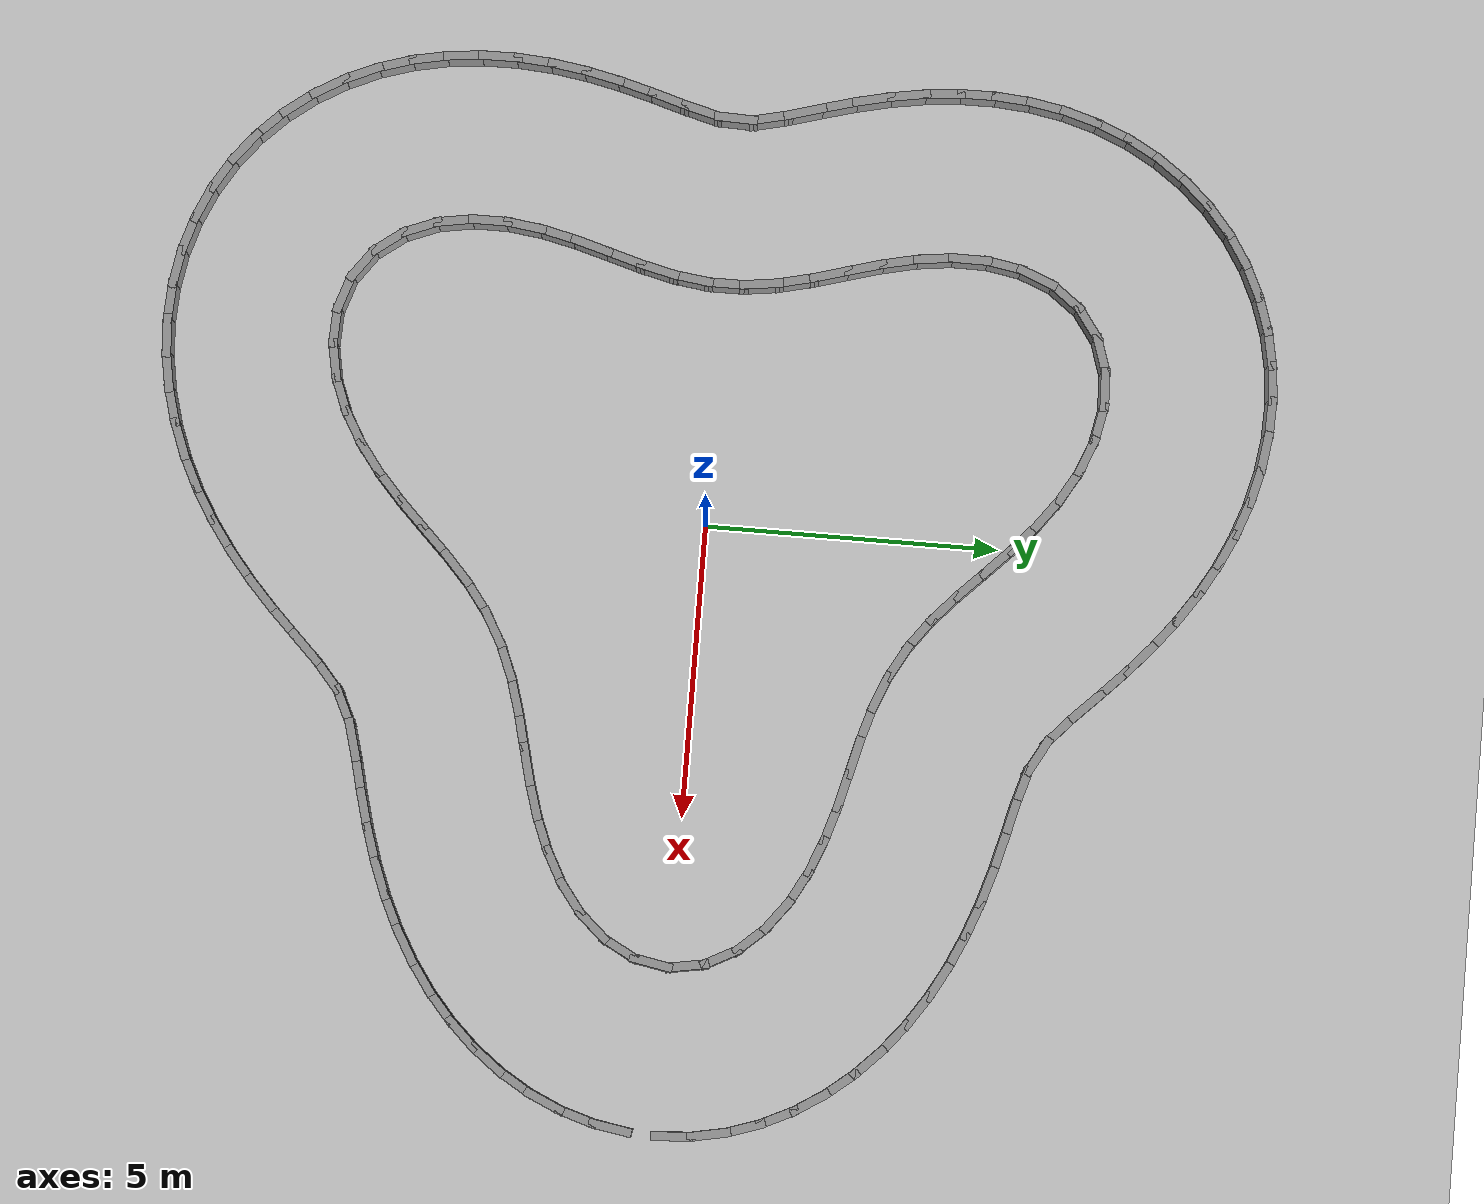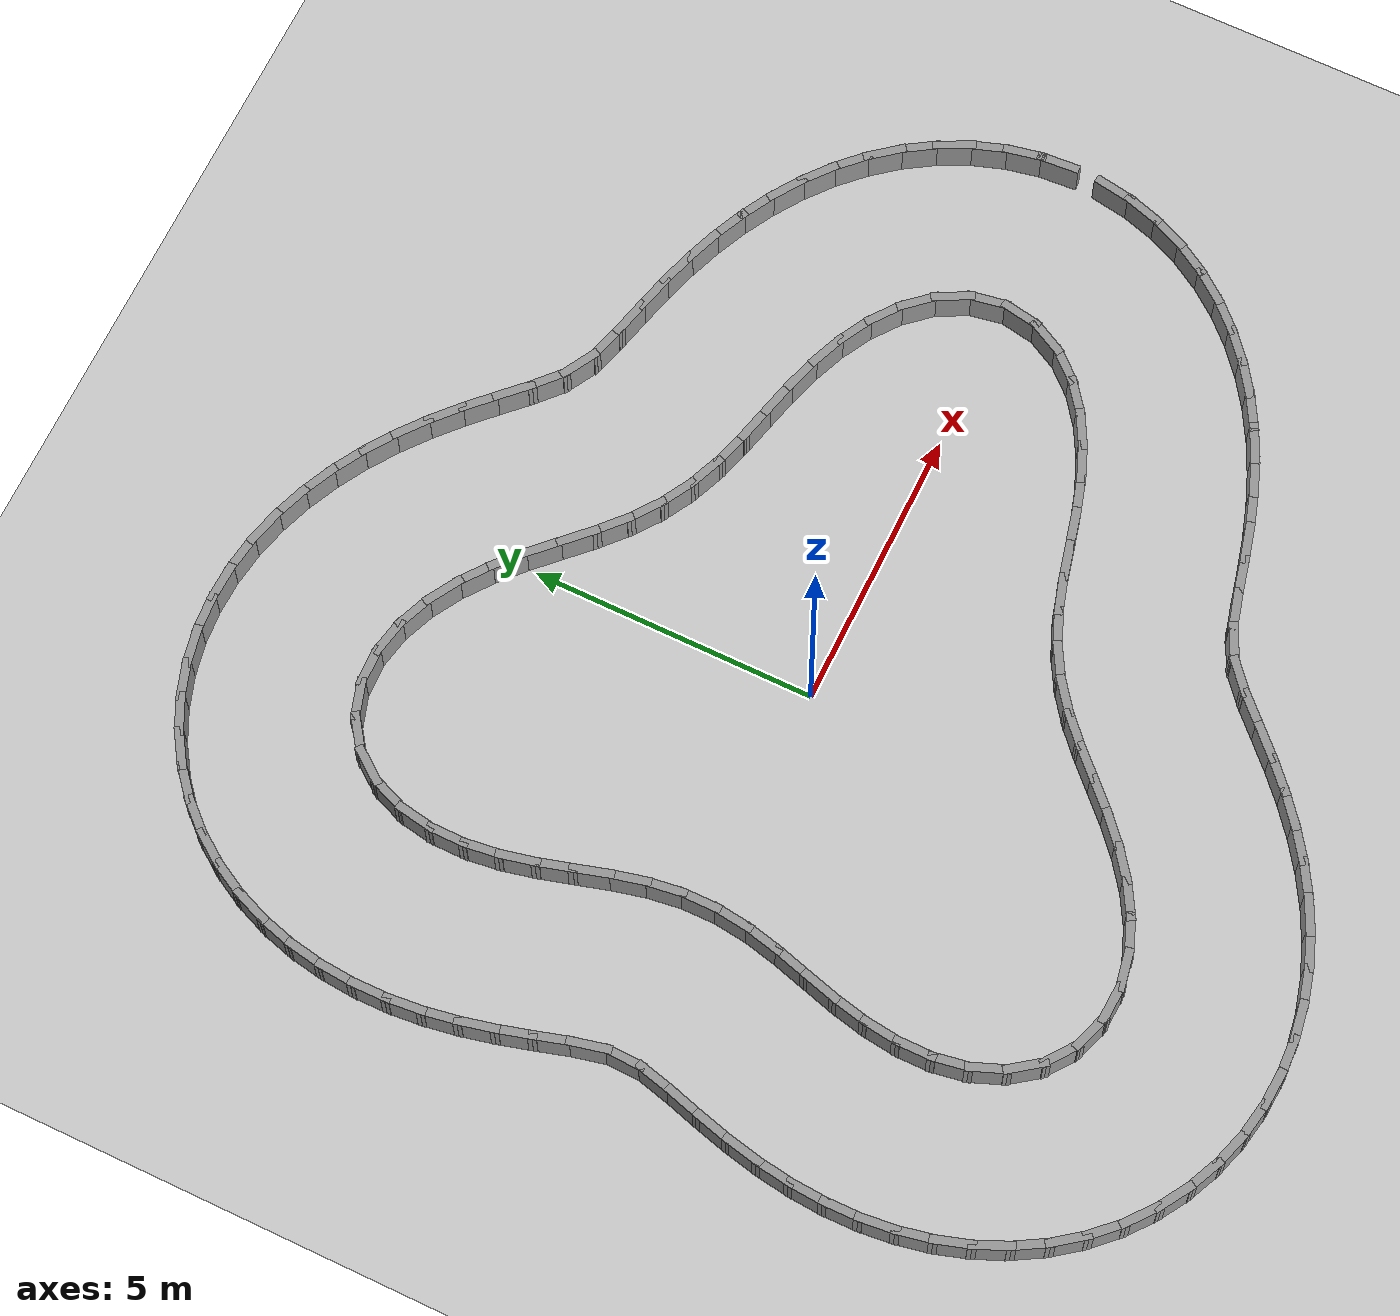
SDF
<?xml version="1.0" ?>
<sdf version='1.7'>
  <world name='default'>
    <plugin name='gazebo_ros_state' filename='libgazebo_ros_state.so'>
      <ros>
        <namespace>/</namespace>
      </ros>
      <update_rate>1000.0</update_rate>
    </plugin>

    <light name='sun' type='directional'>
      <cast_shadows>1</cast_shadows>
      <pose>0 0 10 0 -0 0</pose>
      <diffuse>0.8 0.8 0.8 1</diffuse>
      <specular>0.2 0.2 0.2 1</specular>
      <attenuation>
        <range>1000</range>
        <constant>0.9</constant>
        <linear>0.01</linear>
        <quadratic>0.001</quadratic>
      </attenuation>
      <direction>-0.5 0.1 -0.9</direction>
      <spot>
        <inner_angle>0</inner_angle>
        <outer_angle>0</outer_angle>
        <falloff>0</falloff>
      </spot>
    </light>
    <model name='ground_plane'>
      <static>1</static>
      <link name='link'>
        <collision name='collision'>
          <geometry>
            <plane>
              <normal>0 0 1</normal>
              <size>100 100</size>
            </plane>
          </geometry>
          <surface>
            <friction>
              <ode>
                <mu>100</mu>
                <mu2>50</mu2>
              </ode>
              <torsional>
                <ode/>
              </torsional>
            </friction>
            <contact>
              <ode/>
            </contact>
            <bounce/>
          </surface>
          <max_contacts>10</max_contacts>
        </collision>
        <visual name='visual'>
          <cast_shadows>0</cast_shadows>
          <geometry>
            <plane>
              <normal>0 0 1</normal>
              <size>100 100</size>
            </plane>
          </geometry>
          <material>
            <script>
              <uri>file://media/materials/scripts/gazebo.material</uri>
              <name>Gazebo/Grey</name>
            </script>
          </material>
        </visual>
        <self_collide>0</self_collide>
        <enable_wind>0</enable_wind>
        <kinematic>0</kinematic>
      </link>
    </model>
    <gravity>0 0 -9.8</gravity>
    <magnetic_field>6e-06 2.3e-05 -4.2e-05</magnetic_field>
    <atmosphere type='adiabatic'/>
    <physics type='ode'>
      <max_step_size>0.001</max_step_size>
      <real_time_factor>1</real_time_factor>
      <real_time_update_rate>1000</real_time_update_rate>
    </physics>
    <scene>
      <ambient>0.4 0.4 0.4 1</ambient>
      <background>0.7 0.7 0.7 1</background>
      <shadows>1</shadows>
    </scene>
    <audio>
      <device>default</device>
    </audio>
    <wind/>
    <spherical_coordinates>
      <surface_model>EARTH_WGS84</surface_model>
      <latitude_deg>0</latitude_deg>
      <longitude_deg>0</longitude_deg>
      <elevation>0</elevation>
      <heading_deg>0</heading_deg>
    </spherical_coordinates>
  <model name='rand_lobed_09'>
    <pose>0 0 0 0 -0 0</pose>
    <link name='Wall_0'>
      <collision name='Wall_0_Collision'>
        <geometry><box><size>0.7471 0.1500 0.6000</size></box></geometry>
        <pose>0 0 0.3000 0 -0 0</pose>
      </collision>
      <visual name='Wall_0_Visual'>
        <pose>0 0 0.3000 0 -0 0</pose>
        <geometry><box><size>0.7471 0.1500 0.6000</size></box></geometry>
        <material>
          <script>
            <uri>file://media/materials/scripts/gazebo.material</uri>
            <name>Gazebo/Grey</name>
          </script>
          <ambient>1 1 1 1</ambient>
        </material>
      </visual>
      <pose>7.5078 0.2942 0 0 -0 1.74248</pose>
    </link>
    <link name='Wall_1'>
      <collision name='Wall_1_Collision'>
        <geometry><box><size>0.7480 0.1500 0.6000</size></box></geometry>
        <pose>0 0 0.3000 0 -0 0</pose>
      </collision>
      <visual name='Wall_1_Visual'>
        <pose>0 0 0.3000 0 -0 0</pose>
        <geometry><box><size>0.7480 0.1500 0.6000</size></box></geometry>
        <material>
          <script>
            <uri>file://media/materials/scripts/gazebo.material</uri>
            <name>Gazebo/Grey</name>
          </script>
          <ambient>1 1 1 1</ambient>
        </material>
      </visual>
      <pose>7.3180 0.8532 0 0 -0 2.05335</pose>
    </link>
    <link name='Wall_2'>
      <collision name='Wall_2_Collision'>
        <geometry><box><size>0.7488 0.1500 0.6000</size></box></geometry>
        <pose>0 0 0.3000 0 -0 0</pose>
      </collision>
      <visual name='Wall_2_Visual'>
        <pose>0 0 0.3000 0 -0 0</pose>
        <geometry><box><size>0.7488 0.1500 0.6000</size></box></geometry>
        <material>
          <script>
            <uri>file://media/materials/scripts/gazebo.material</uri>
            <name>Gazebo/Grey</name>
          </script>
          <ambient>1 1 1 1</ambient>
        </material>
      </visual>
      <pose>6.9795 1.3411 0 0 -0 2.30128</pose>
    </link>
    <link name='Wall_3'>
      <collision name='Wall_3_Collision'>
        <geometry><box><size>0.7493 0.1500 0.6000</size></box></geometry>
        <pose>0 0 0.3000 0 -0 0</pose>
      </collision>
      <visual name='Wall_3_Visual'>
        <pose>0 0 0.3000 0 -0 0</pose>
        <geometry><box><size>0.7493 0.1500 0.6000</size></box></geometry>
        <material>
          <script>
            <uri>file://media/materials/scripts/gazebo.material</uri>
            <name>Gazebo/Grey</name>
          </script>
          <ambient>1 1 1 1</ambient>
        </material>
      </visual>
      <pose>6.5408 1.7450 0 0 -0 2.49363</pose>
    </link>
    <link name='Wall_4'>
      <collision name='Wall_4_Collision'>
        <geometry><box><size>0.7496 0.1500 0.6000</size></box></geometry>
        <pose>0 0 0.3000 0 -0 0</pose>
      </collision>
      <visual name='Wall_4_Visual'>
        <pose>0 0 0.3000 0 -0 0</pose>
        <geometry><box><size>0.7496 0.1500 0.6000</size></box></geometry>
        <material>
          <script>
            <uri>file://media/materials/scripts/gazebo.material</uri>
            <name>Gazebo/Grey</name>
          </script>
          <ambient>1 1 1 1</ambient>
        </material>
      </visual>
      <pose>6.0385 2.0689 0 0 -0 2.64404</pose>
    </link>
    <link name='Wall_5'>
      <collision name='Wall_5_Collision'>
        <geometry><box><size>0.7497 0.1500 0.6000</size></box></geometry>
        <pose>0 0 0.3000 0 -0 0</pose>
      </collision>
      <visual name='Wall_5_Visual'>
        <pose>0 0 0.3000 0 -0 0</pose>
        <geometry><box><size>0.7497 0.1500 0.6000</size></box></geometry>
        <material>
          <script>
            <uri>file://media/materials/scripts/gazebo.material</uri>
            <name>Gazebo/Grey</name>
          </script>
          <ambient>1 1 1 1</ambient>
        </material>
      </visual>
      <pose>5.4967 2.3235 0 0 -0 2.76055</pose>
    </link>
    <link name='Wall_6'>
      <collision name='Wall_6_Collision'>
        <geometry><box><size>0.7499 0.1500 0.6000</size></box></geometry>
        <pose>0 0 0.3000 0 -0 0</pose>
      </collision>
      <visual name='Wall_6_Visual'>
        <pose>0 0 0.3000 0 -0 0</pose>
        <geometry><box><size>0.7499 0.1500 0.6000</size></box></geometry>
        <material>
          <script>
            <uri>file://media/materials/scripts/gazebo.material</uri>
            <name>Gazebo/Grey</name>
          </script>
          <ambient>1 1 1 1</ambient>
        </material>
      </visual>
      <pose>4.9315 2.5226 0 0 -0 2.84526</pose>
    </link>
    <link name='Wall_7'>
      <collision name='Wall_7_Collision'>
        <geometry><box><size>0.7500 0.1500 0.6000</size></box></geometry>
        <pose>0 0 0.3000 0 -0 0</pose>
      </collision>
      <visual name='Wall_7_Visual'>
        <pose>0 0 0.3000 0 -0 0</pose>
        <geometry><box><size>0.7500 0.1500 0.6000</size></box></geometry>
        <material>
          <script>
            <uri>file://media/materials/scripts/gazebo.material</uri>
            <name>Gazebo/Grey</name>
          </script>
          <ambient>1 1 1 1</ambient>
        </material>
      </visual>
      <pose>4.3537 2.6837 0 0 -0 2.89428</pose>
    </link>
    <link name='Wall_8'>
      <collision name='Wall_8_Collision'>
        <geometry><box><size>0.7500 0.1500 0.6000</size></box></geometry>
        <pose>0 0 0.3000 0 -0 0</pose>
      </collision>
      <visual name='Wall_8_Visual'>
        <pose>0 0 0.3000 0 -0 0</pose>
        <geometry><box><size>0.7500 0.1500 0.6000</size></box></geometry>
        <material>
          <script>
            <uri>file://media/materials/scripts/gazebo.material</uri>
            <name>Gazebo/Grey</name>
          </script>
          <ambient>1 1 1 1</ambient>
        </material>
      </visual>
      <pose>3.7717 2.8291 0 0 -0 2.89908</pose>
    </link>
    <link name='Wall_9'>
      <collision name='Wall_9_Collision'>
        <geometry><box><size>0.7499 0.1500 0.6000</size></box></geometry>
        <pose>0 0 0.3000 0 -0 0</pose>
      </collision>
      <visual name='Wall_9_Visual'>
        <pose>0 0 0.3000 0 -0 0</pose>
        <geometry><box><size>0.7499 0.1500 0.6000</size></box></geometry>
        <material>
          <script>
            <uri>file://media/materials/scripts/gazebo.material</uri>
            <name>Gazebo/Grey</name>
          </script>
          <ambient>1 1 1 1</ambient>
        </material>
      </visual>
      <pose>3.1930 2.9868 0 0 -0 2.85210</pose>
    </link>
    <link name='Wall_10'>
      <collision name='Wall_10_Collision'>
        <geometry><box><size>0.7497 0.1500 0.6000</size></box></geometry>
        <pose>0 0 0.3000 0 -0 0</pose>
      </collision>
      <visual name='Wall_10_Visual'>
        <pose>0 0 0.3000 0 -0 0</pose>
        <geometry><box><size>0.7497 0.1500 0.6000</size></box></geometry>
        <material>
          <script>
            <uri>file://media/materials/scripts/gazebo.material</uri>
            <name>Gazebo/Grey</name>
          </script>
          <ambient>1 1 1 1</ambient>
        </material>
      </visual>
      <pose>2.6277 3.1850 0 0 -0 2.75660</pose>
    </link>
    <link name='Wall_11'>
      <collision name='Wall_11_Collision'>
        <geometry><box><size>0.7496 0.1500 0.6000</size></box></geometry>
        <pose>0 0 0.3000 0 -0 0</pose>
      </collision>
      <visual name='Wall_11_Visual'>
        <pose>0 0 0.3000 0 -0 0</pose>
        <geometry><box><size>0.7496 0.1500 0.6000</size></box></geometry>
        <material>
          <script>
            <uri>file://media/materials/scripts/gazebo.material</uri>
            <name>Gazebo/Grey</name>
          </script>
          <ambient>1 1 1 1</ambient>
        </material>
      </visual>
      <pose>2.0882 3.4440 0 0 -0 2.63130</pose>
    </link>
    <link name='Wall_12'>
      <collision name='Wall_12_Collision'>
        <geometry><box><size>0.7497 0.1500 0.6000</size></box></geometry>
        <pose>0 0 0.3000 0 -0 0</pose>
      </collision>
      <visual name='Wall_12_Visual'>
        <pose>0 0 0.3000 0 -0 0</pose>
        <geometry><box><size>0.7497 0.1500 0.6000</size></box></geometry>
        <material>
          <script>
            <uri>file://media/materials/scripts/gazebo.material</uri>
            <name>Gazebo/Grey</name>
          </script>
          <ambient>1 1 1 1</ambient>
        </material>
      </visual>
      <pose>1.5855 3.7688 0 0 -0 2.50470</pose>
    </link>
    <link name='Wall_13'>
      <collision name='Wall_13_Collision'>
        <geometry><box><size>0.7499 0.1500 0.6000</size></box></geometry>
        <pose>0 0 0.3000 0 -0 0</pose>
      </collision>
      <visual name='Wall_13_Visual'>
        <pose>0 0 0.3000 0 -0 0</pose>
        <geometry><box><size>0.7499 0.1500 0.6000</size></box></geometry>
        <material>
          <script>
            <uri>file://media/materials/scripts/gazebo.material</uri>
            <name>Gazebo/Grey</name>
          </script>
          <ambient>1 1 1 1</ambient>
        </material>
      </visual>
      <pose>1.1221 4.1483 0 0 -0 2.40606</pose>
    </link>
    <link name='Wall_14'>
      <collision name='Wall_14_Collision'>
        <geometry><box><size>0.7500 0.1500 0.6000</size></box></geometry>
        <pose>0 0 0.3000 0 -0 0</pose>
      </collision>
      <visual name='Wall_14_Visual'>
        <pose>0 0 0.3000 0 -0 0</pose>
        <geometry><box><size>0.7500 0.1500 0.6000</size></box></geometry>
        <material>
          <script>
            <uri>file://media/materials/scripts/gazebo.material</uri>
            <name>Gazebo/Grey</name>
          </script>
          <ambient>1 1 1 1</ambient>
        </material>
      </visual>
      <pose>0.6876 4.5617 0 0 -0 2.35609</pose>
    </link>
    <link name='Wall_15'>
      <collision name='Wall_15_Collision'>
        <geometry><box><size>0.7500 0.1500 0.6000</size></box></geometry>
        <pose>0 0 0.3000 0 -0 0</pose>
      </collision>
      <visual name='Wall_15_Visual'>
        <pose>0 0 0.3000 0 -0 0</pose>
        <geometry><box><size>0.7500 0.1500 0.6000</size></box></geometry>
        <material>
          <script>
            <uri>file://media/materials/scripts/gazebo.material</uri>
            <name>Gazebo/Grey</name>
          </script>
          <ambient>1 1 1 1</ambient>
        </material>
      </visual>
      <pose>0.2626 4.9852 0 0 -0 2.35991</pose>
    </link>
    <link name='Wall_16'>
      <collision name='Wall_16_Collision'>
        <geometry><box><size>0.7499 0.1500 0.6000</size></box></geometry>
        <pose>0 0 0.3000 0 -0 0</pose>
      </collision>
      <visual name='Wall_16_Visual'>
        <pose>0 0 0.3000 0 -0 0</pose>
        <geometry><box><size>0.7499 0.1500 0.6000</size></box></geometry>
        <material>
          <script>
            <uri>file://media/materials/scripts/gazebo.material</uri>
            <name>Gazebo/Grey</name>
          </script>
          <ambient>1 1 1 1</ambient>
        </material>
      </visual>
      <pose>-0.1735 5.3969 0 0 -0 2.41019</pose>
    </link>
    <link name='Wall_17'>
      <collision name='Wall_17_Collision'>
        <geometry><box><size>0.7497 0.1500 0.6000</size></box></geometry>
        <pose>0 0 0.3000 0 -0 0</pose>
      </collision>
      <visual name='Wall_17_Visual'>
        <pose>0 0 0.3000 0 -0 0</pose>
        <geometry><box><size>0.7497 0.1500 0.6000</size></box></geometry>
        <material>
          <script>
            <uri>file://media/materials/scripts/gazebo.material</uri>
            <name>Gazebo/Grey</name>
          </script>
          <ambient>1 1 1 1</ambient>
        </material>
      </visual>
      <pose>-0.6365 5.7773 0 0 -0 2.49728</pose>
    </link>
    <link name='Wall_18'>
      <collision name='Wall_18_Collision'>
        <geometry><box><size>0.7496 0.1500 0.6000</size></box></geometry>
        <pose>0 0 0.3000 0 -0 0</pose>
      </collision>
      <visual name='Wall_18_Visual'>
        <pose>0 0 0.3000 0 -0 0</pose>
        <geometry><box><size>0.7496 0.1500 0.6000</size></box></geometry>
        <material>
          <script>
            <uri>file://media/materials/scripts/gazebo.material</uri>
            <name>Gazebo/Grey</name>
          </script>
          <ambient>1 1 1 1</ambient>
        </material>
      </visual>
      <pose>-1.1355 6.1080 0 0 -0 2.61554</pose>
    </link>
    <link name='Wall_19'>
      <collision name='Wall_19_Collision'>
        <geometry><box><size>0.7493 0.1500 0.6000</size></box></geometry>
        <pose>0 0 0.3000 0 -0 0</pose>
      </collision>
      <visual name='Wall_19_Visual'>
        <pose>0 0 0.3000 0 -0 0</pose>
        <geometry><box><size>0.7493 0.1500 0.6000</size></box></geometry>
        <material>
          <script>
            <uri>file://media/materials/scripts/gazebo.material</uri>
            <name>Gazebo/Grey</name>
          </script>
          <ambient>1 1 1 1</ambient>
        </material>
      </visual>
      <pose>-1.6734 6.3688 0 0 -0 2.76470</pose>
    </link>
    <link name='Wall_20'>
      <collision name='Wall_20_Collision'>
        <geometry><box><size>0.7490 0.1500 0.6000</size></box></geometry>
        <pose>0 0 0.3000 0 -0 0</pose>
      </collision>
      <visual name='Wall_20_Visual'>
        <pose>0 0 0.3000 0 -0 0</pose>
        <geometry><box><size>0.7490 0.1500 0.6000</size></box></geometry>
        <material>
          <script>
            <uri>file://media/materials/scripts/gazebo.material</uri>
            <name>Gazebo/Grey</name>
          </script>
          <ambient>1 1 1 1</ambient>
        </material>
      </visual>
      <pose>-2.2459 6.5364 0 0 -0 2.94902</pose>
    </link>
    <link name='Wall_21'>
      <collision name='Wall_21_Collision'>
        <geometry><box><size>0.7484 0.1500 0.6000</size></box></geometry>
        <pose>0 0 0.3000 0 -0 0</pose>
      </collision>
      <visual name='Wall_21_Visual'>
        <pose>0 0 0.3000 0 -0 0</pose>
        <geometry><box><size>0.7484 0.1500 0.6000</size></box></geometry>
        <material>
          <script>
            <uri>file://media/materials/scripts/gazebo.material</uri>
            <name>Gazebo/Grey</name>
          </script>
          <ambient>1 1 1 1</ambient>
        </material>
      </visual>
      <pose>-2.8389 6.5833 0 0 -0 -3.10686</pose>
    </link>
    <link name='Wall_22'>
      <collision name='Wall_22_Collision'>
        <geometry><box><size>0.7478 0.1500 0.6000</size></box></geometry>
        <pose>0 0 0.3000 0 -0 0</pose>
      </collision>
      <visual name='Wall_22_Visual'>
        <pose>0 0 0.3000 0 -0 0</pose>
        <geometry><box><size>0.7478 0.1500 0.6000</size></box></geometry>
        <material>
          <script>
            <uri>file://media/materials/scripts/gazebo.material</uri>
            <name>Gazebo/Grey</name>
          </script>
          <ambient>1 1 1 1</ambient>
        </material>
      </visual>
      <pose>-3.4226 6.4817 0 0 -0 -2.83146</pose>
    </link>
    <link name='Wall_23'>
      <collision name='Wall_23_Collision'>
        <geometry><box><size>0.7475 0.1500 0.6000</size></box></geometry>
        <pose>0 0 0.3000 0 -0 0</pose>
      </collision>
      <visual name='Wall_23_Visual'>
        <pose>0 0 0.3000 0 -0 0</pose>
        <geometry><box><size>0.7475 0.1500 0.6000</size></box></geometry>
        <material>
          <script>
            <uri>file://media/materials/scripts/gazebo.material</uri>
            <name>Gazebo/Grey</name>
          </script>
          <ambient>1 1 1 1</ambient>
        </material>
      </visual>
      <pose>-3.9504 6.2169 0 0 -0 -2.52177</pose>
    </link>
    <link name='Wall_24'>
      <collision name='Wall_24_Collision'>
        <geometry><box><size>0.7479 0.1500 0.6000</size></box></geometry>
        <pose>0 0 0.3000 0 -0 0</pose>
      </collision>
      <visual name='Wall_24_Visual'>
        <pose>0 0 0.3000 0 -0 0</pose>
        <geometry><box><size>0.7479 0.1500 0.6000</size></box></geometry>
        <material>
          <script>
            <uri>file://media/materials/scripts/gazebo.material</uri>
            <name>Gazebo/Grey</name>
          </script>
          <ambient>1 1 1 1</ambient>
        </material>
      </visual>
      <pose>-4.3738 5.8048 0 0 -0 -2.21781</pose>
    </link>
    <link name='Wall_25'>
      <collision name='Wall_25_Collision'>
        <geometry><box><size>0.7486 0.1500 0.6000</size></box></geometry>
        <pose>0 0 0.3000 0 -0 0</pose>
      </collision>
      <visual name='Wall_25_Visual'>
        <pose>0 0 0.3000 0 -0 0</pose>
        <geometry><box><size>0.7486 0.1500 0.6000</size></box></geometry>
        <material>
          <script>
            <uri>file://media/materials/scripts/gazebo.material</uri>
            <name>Gazebo/Grey</name>
          </script>
          <ambient>1 1 1 1</ambient>
        </material>
      </visual>
      <pose>-4.6664 5.2889 0 0 -0 -1.95575</pose>
    </link>
    <link name='Wall_26'>
      <collision name='Wall_26_Collision'>
        <geometry><box><size>0.7491 0.1500 0.6000</size></box></geometry>
        <pose>0 0 0.3000 0 -0 0</pose>
      </collision>
      <visual name='Wall_26_Visual'>
        <pose>0 0 0.3000 0 -0 0</pose>
        <geometry><box><size>0.7491 0.1500 0.6000</size></box></geometry>
        <material>
          <script>
            <uri>file://media/materials/scripts/gazebo.material</uri>
            <name>Gazebo/Grey</name>
          </script>
          <ambient>1 1 1 1</ambient>
        </material>
      </visual>
      <pose>-4.8304 4.7164 0 0 -0 -1.74390</pose>
    </link>
    <link name='Wall_27'>
      <collision name='Wall_27_Collision'>
        <geometry><box><size>0.7494 0.1500 0.6000</size></box></geometry>
        <pose>0 0 0.3000 0 -0 0</pose>
      </collision>
      <visual name='Wall_27_Visual'>
        <pose>0 0 0.3000 0 -0 0</pose>
        <geometry><box><size>0.7494 0.1500 0.6000</size></box></geometry>
        <material>
          <script>
            <uri>file://media/materials/scripts/gazebo.material</uri>
            <name>Gazebo/Grey</name>
          </script>
          <ambient>1 1 1 1</ambient>
        </material>
      </visual>
      <pose>-4.8835 4.1216 0 0 -0 -1.57599</pose>
    </link>
    <link name='Wall_28'>
      <collision name='Wall_28_Collision'>
        <geometry><box><size>0.7497 0.1500 0.6000</size></box></geometry>
        <pose>0 0 0.3000 0 -0 0</pose>
      </collision>
      <visual name='Wall_28_Visual'>
        <pose>0 0 0.3000 0 -0 0</pose>
        <geometry><box><size>0.7497 0.1500 0.6000</size></box></geometry>
        <material>
          <script>
            <uri>file://media/materials/scripts/gazebo.material</uri>
            <name>Gazebo/Grey</name>
          </script>
          <ambient>1 1 1 1</ambient>
        </material>
      </visual>
      <pose>-4.8476 3.5244 0 0 -0 -1.44555</pose>
    </link>
    <link name='Wall_29'>
      <collision name='Wall_29_Collision'>
        <geometry><box><size>0.7499 0.1500 0.6000</size></box></geometry>
        <pose>0 0 0.3000 0 -0 0</pose>
      </collision>
      <visual name='Wall_29_Visual'>
        <pose>0 0 0.3000 0 -0 0</pose>
        <geometry><box><size>0.7499 0.1500 0.6000</size></box></geometry>
        <material>
          <script>
            <uri>file://media/materials/scripts/gazebo.material</uri>
            <name>Gazebo/Grey</name>
          </script>
          <ambient>1 1 1 1</ambient>
        </material>
      </visual>
      <pose>-4.7447 2.9342 0 0 -0 -1.35069</pose>
    </link>
    <link name='Wall_30'>
      <collision name='Wall_30_Collision'>
        <geometry><box><size>0.7500 0.1500 0.6000</size></box></geometry>
        <pose>0 0 0.3000 0 -0 0</pose>
      </collision>
      <visual name='Wall_30_Visual'>
        <pose>0 0 0.3000 0 -0 0</pose>
        <geometry><box><size>0.7500 0.1500 0.6000</size></box></geometry>
        <material>
          <script>
            <uri>file://media/materials/scripts/gazebo.material</uri>
            <name>Gazebo/Grey</name>
          </script>
          <ambient>1 1 1 1</ambient>
        </material>
      </visual>
      <pose>-4.5976 2.3529 0 0 -0 -1.29547</pose>
    </link>
    <link name='Wall_31'>
      <collision name='Wall_31_Collision'>
        <geometry><box><size>0.7500 0.1500 0.6000</size></box></geometry>
        <pose>0 0 0.3000 0 -0 0</pose>
      </collision>
      <visual name='Wall_31_Visual'>
        <pose>0 0 0.3000 0 -0 0</pose>
        <geometry><box><size>0.7500 0.1500 0.6000</size></box></geometry>
        <material>
          <script>
            <uri>file://media/materials/scripts/gazebo.material</uri>
            <name>Gazebo/Grey</name>
          </script>
          <ambient>1 1 1 1</ambient>
        </material>
      </visual>
      <pose>-4.4326 1.7760 0 0 -0 -1.28864</pose>
    </link>
    <link name='Wall_32'>
      <collision name='Wall_32_Collision'>
        <geometry><box><size>0.7499 0.1500 0.6000</size></box></geometry>
        <pose>0 0 0.3000 0 -0 0</pose>
      </collision>
      <visual name='Wall_32_Visual'>
        <pose>0 0 0.3000 0 -0 0</pose>
        <geometry><box><size>0.7499 0.1500 0.6000</size></box></geometry>
        <material>
          <script>
            <uri>file://media/materials/scripts/gazebo.material</uri>
            <name>Gazebo/Grey</name>
          </script>
          <ambient>1 1 1 1</ambient>
        </material>
      </visual>
      <pose>-4.2797 1.1961 0 0 -0 -1.33762</pose>
    </link>
    <link name='Wall_33'>
      <collision name='Wall_33_Collision'>
        <geometry><box><size>0.7496 0.1500 0.6000</size></box></geometry>
        <pose>0 0 0.3000 0 -0 0</pose>
      </collision>
      <visual name='Wall_33_Visual'>
        <pose>0 0 0.3000 0 -0 0</pose>
        <geometry><box><size>0.7496 0.1500 0.6000</size></box></geometry>
        <material>
          <script>
            <uri>file://media/materials/scripts/gazebo.material</uri>
            <name>Gazebo/Grey</name>
          </script>
          <ambient>1 1 1 1</ambient>
        </material>
      </visual>
      <pose>-4.1707 0.6071 0 0 -0 -1.43780</pose>
    </link>
    <link name='Wall_34'>
      <collision name='Wall_34_Collision'>
        <geometry><box><size>0.7495 0.1500 0.6000</size></box></geometry>
        <pose>0 0 0.3000 0 -0 0</pose>
      </collision>
      <visual name='Wall_34_Visual'>
        <pose>0 0 0.3000 0 -0 0</pose>
        <geometry><box><size>0.7495 0.1500 0.6000</size></box></geometry>
        <material>
          <script>
            <uri>file://media/materials/scripts/gazebo.material</uri>
            <name>Gazebo/Grey</name>
          </script>
          <ambient>1 1 1 1</ambient>
        </material>
      </visual>
      <pose>-4.1302 0.0102 0 0 -0 -1.56844</pose>
    </link>
    <link name='Wall_35'>
      <collision name='Wall_35_Collision'>
        <geometry><box><size>0.7496 0.1500 0.6000</size></box></geometry>
        <pose>0 0 0.3000 0 -0 0</pose>
      </collision>
      <visual name='Wall_35_Visual'>
        <pose>0 0 0.3000 0 -0 0</pose>
        <geometry><box><size>0.7496 0.1500 0.6000</size></box></geometry>
        <material>
          <script>
            <uri>file://media/materials/scripts/gazebo.material</uri>
            <name>Gazebo/Grey</name>
          </script>
          <ambient>1 1 1 1</ambient>
        </material>
      </visual>
      <pose>-4.1681 -0.5869 0 0 -0 -1.69973</pose>
    </link>
    <link name='Wall_36'>
      <collision name='Wall_36_Collision'>
        <geometry><box><size>0.7498 0.1500 0.6000</size></box></geometry>
        <pose>0 0 0.3000 0 -0 0</pose>
      </collision>
      <visual name='Wall_36_Visual'>
        <pose>0 0 0.3000 0 -0 0</pose>
        <geometry><box><size>0.7498 0.1500 0.6000</size></box></geometry>
        <material>
          <script>
            <uri>file://media/materials/scripts/gazebo.material</uri>
            <name>Gazebo/Grey</name>
          </script>
          <ambient>1 1 1 1</ambient>
        </material>
      </visual>
      <pose>-4.2751 -1.1762 0 0 -0 -1.80134</pose>
    </link>
    <link name='Wall_37'>
      <collision name='Wall_37_Collision'>
        <geometry><box><size>0.7500 0.1500 0.6000</size></box></geometry>
        <pose>0 0 0.3000 0 -0 0</pose>
      </collision>
      <visual name='Wall_37_Visual'>
        <pose>0 0 0.3000 0 -0 0</pose>
        <geometry><box><size>0.7500 0.1500 0.6000</size></box></geometry>
        <material>
          <script>
            <uri>file://media/materials/scripts/gazebo.material</uri>
            <name>Gazebo/Grey</name>
          </script>
          <ambient>1 1 1 1</ambient>
        </material>
      </visual>
      <pose>-4.4270 -1.7564 0 0 -0 -1.85222</pose>
    </link>
    <link name='Wall_38'>
      <collision name='Wall_38_Collision'>
        <geometry><box><size>0.7500 0.1500 0.6000</size></box></geometry>
        <pose>0 0 0.3000 0 -0 0</pose>
      </collision>
      <visual name='Wall_38_Visual'>
        <pose>0 0 0.3000 0 -0 0</pose>
        <geometry><box><size>0.7500 0.1500 0.6000</size></box></geometry>
        <material>
          <script>
            <uri>file://media/materials/scripts/gazebo.material</uri>
            <name>Gazebo/Grey</name>
          </script>
          <ambient>1 1 1 1</ambient>
        </material>
      </visual>
      <pose>-4.5922 -2.3332 0 0 -0 -1.84720</pose>
    </link>
    <link name='Wall_39'>
      <collision name='Wall_39_Collision'>
        <geometry><box><size>0.7499 0.1500 0.6000</size></box></geometry>
        <pose>0 0 0.3000 0 -0 0</pose>
      </collision>
      <visual name='Wall_39_Visual'>
        <pose>0 0 0.3000 0 -0 0</pose>
        <geometry><box><size>0.7499 0.1500 0.6000</size></box></geometry>
        <material>
          <script>
            <uri>file://media/materials/scripts/gazebo.material</uri>
            <name>Gazebo/Grey</name>
          </script>
          <ambient>1 1 1 1</ambient>
        </material>
      </visual>
      <pose>-4.7403 -2.9143 0 0 -0 -1.79349</pose>
    </link>
    <link name='Wall_40'>
      <collision name='Wall_40_Collision'>
        <geometry><box><size>0.7497 0.1500 0.6000</size></box></geometry>
        <pose>0 0 0.3000 0 -0 0</pose>
      </collision>
      <visual name='Wall_40_Visual'>
        <pose>0 0 0.3000 0 -0 0</pose>
        <geometry><box><size>0.7497 0.1500 0.6000</size></box></geometry>
        <material>
          <script>
            <uri>file://media/materials/scripts/gazebo.material</uri>
            <name>Gazebo/Grey</name>
          </script>
          <ambient>1 1 1 1</ambient>
        </material>
      </visual>
      <pose>-4.8451 -3.5042 0 0 -0 -1.69987</pose>
    </link>
    <link name='Wall_41'>
      <collision name='Wall_41_Collision'>
        <geometry><box><size>0.7495 0.1500 0.6000</size></box></geometry>
        <pose>0 0 0.3000 0 -0 0</pose>
      </collision>
      <visual name='Wall_41_Visual'>
        <pose>0 0 0.3000 0 -0 0</pose>
        <geometry><box><size>0.7495 0.1500 0.6000</size></box></geometry>
        <material>
          <script>
            <uri>file://media/materials/scripts/gazebo.material</uri>
            <name>Gazebo/Grey</name>
          </script>
          <ambient>1 1 1 1</ambient>
        </material>
      </visual>
      <pose>-4.8837 -4.1013 0 0 -0 -1.57063</pose>
    </link>
    <link name='Wall_42'>
      <collision name='Wall_42_Collision'>
        <geometry><box><size>0.7491 0.1500 0.6000</size></box></geometry>
        <pose>0 0 0.3000 0 -0 0</pose>
      </collision>
      <visual name='Wall_42_Visual'>
        <pose>0 0 0.3000 0 -0 0</pose>
        <geometry><box><size>0.7491 0.1500 0.6000</size></box></geometry>
        <material>
          <script>
            <uri>file://media/materials/scripts/gazebo.material</uri>
            <name>Gazebo/Grey</name>
          </script>
          <ambient>1 1 1 1</ambient>
        </material>
      </visual>
      <pose>-4.8339 -4.6964 0 0 -0 -1.40405</pose>
    </link>
    <link name='Wall_43'>
      <collision name='Wall_43_Collision'>
        <geometry><box><size>0.7486 0.1500 0.6000</size></box></geometry>
        <pose>0 0 0.3000 0 -0 0</pose>
      </collision>
      <visual name='Wall_43_Visual'>
        <pose>0 0 0.3000 0 -0 0</pose>
        <geometry><box><size>0.7486 0.1500 0.6000</size></box></geometry>
        <material>
          <script>
            <uri>file://media/materials/scripts/gazebo.material</uri>
            <name>Gazebo/Grey</name>
          </script>
          <ambient>1 1 1 1</ambient>
        </material>
      </visual>
      <pose>-4.6740 -5.2701 0 0 -0 -1.19387</pose>
    </link>
    <link name='Wall_44'>
      <collision name='Wall_44_Collision'>
        <geometry><box><size>0.7480 0.1500 0.6000</size></box></geometry>
        <pose>0 0 0.3000 0 -0 0</pose>
      </collision>
      <visual name='Wall_44_Visual'>
        <pose>0 0 0.3000 0 -0 0</pose>
        <geometry><box><size>0.7480 0.1500 0.6000</size></box></geometry>
        <material>
          <script>
            <uri>file://media/materials/scripts/gazebo.material</uri>
            <name>Gazebo/Grey</name>
          </script>
          <ambient>1 1 1 1</ambient>
        </material>
      </visual>
      <pose>-4.3859 -5.7887 0 0 -0 -0.93351</pose>
    </link>
    <link name='Wall_45'>
      <collision name='Wall_45_Collision'>
        <geometry><box><size>0.7475 0.1500 0.6000</size></box></geometry>
        <pose>0 0 0.3000 0 -0 0</pose>
      </collision>
      <visual name='Wall_45_Visual'>
        <pose>0 0 0.3000 0 -0 0</pose>
        <geometry><box><size>0.7475 0.1500 0.6000</size></box></geometry>
        <material>
          <script>
            <uri>file://media/materials/scripts/gazebo.material</uri>
            <name>Gazebo/Grey</name>
          </script>
          <ambient>1 1 1 1</ambient>
        </material>
      </visual>
      <pose>-3.9667 -6.2051 0 0 -0 -0.63054</pose>
    </link>
    <link name='Wall_46'>
      <collision name='Wall_46_Collision'>
        <geometry><box><size>0.7478 0.1500 0.6000</size></box></geometry>
        <pose>0 0 0.3000 0 -0 0</pose>
      </collision>
      <visual name='Wall_46_Visual'>
        <pose>0 0 0.3000 0 -0 0</pose>
        <geometry><box><size>0.7478 0.1500 0.6000</size></box></geometry>
        <material>
          <script>
            <uri>file://media/materials/scripts/gazebo.material</uri>
            <name>Gazebo/Grey</name>
          </script>
          <ambient>1 1 1 1</ambient>
        </material>
      </visual>
      <pose>-3.4417 -6.4754 0 0 -0 -0.32027</pose>
    </link>
    <link name='Wall_47'>
      <collision name='Wall_47_Collision'>
        <geometry><box><size>0.7484 0.1500 0.6000</size></box></geometry>
        <pose>0 0 0.3000 0 -0 0</pose>
      </collision>
      <visual name='Wall_47_Visual'>
        <pose>0 0 0.3000 0 -0 0</pose>
        <geometry><box><size>0.7484 0.1500 0.6000</size></box></geometry>
        <material>
          <script>
            <uri>file://media/materials/scripts/gazebo.material</uri>
            <name>Gazebo/Grey</name>
          </script>
          <ambient>1 1 1 1</ambient>
        </material>
      </visual>
      <pose>-2.8591 -6.5824 0 0 -0 -0.04329</pose>
    </link>
    <link name='Wall_48'>
      <collision name='Wall_48_Collision'>
        <geometry><box><size>0.7489 0.1500 0.6000</size></box></geometry>
        <pose>0 0 0.3000 0 -0 0</pose>
      </collision>
      <visual name='Wall_48_Visual'>
        <pose>0 0 0.3000 0 -0 0</pose>
        <geometry><box><size>0.7489 0.1500 0.6000</size></box></geometry>
        <material>
          <script>
            <uri>file://media/materials/scripts/gazebo.material</uri>
            <name>Gazebo/Grey</name>
          </script>
          <ambient>1 1 1 1</ambient>
        </material>
      </visual>
      <pose>-2.2659 -6.5401 0 0 -0 0.18554</pose>
    </link>
    <link name='Wall_49'>
      <collision name='Wall_49_Collision'>
        <geometry><box><size>0.7493 0.1500 0.6000</size></box></geometry>
        <pose>0 0 0.3000 0 -0 0</pose>
      </collision>
      <visual name='Wall_49_Visual'>
        <pose>0 0 0.3000 0 -0 0</pose>
        <geometry><box><size>0.7493 0.1500 0.6000</size></box></geometry>
        <material>
          <script>
            <uri>file://media/materials/scripts/gazebo.material</uri>
            <name>Gazebo/Grey</name>
          </script>
          <ambient>1 1 1 1</ambient>
        </material>
      </visual>
      <pose>-1.6923 -6.3761 0 0 -0 0.37130</pose>
    </link>
    <link name='Wall_50'>
      <collision name='Wall_50_Collision'>
        <geometry><box><size>0.7495 0.1500 0.6000</size></box></geometry>
        <pose>0 0 0.3000 0 -0 0</pose>
      </collision>
      <visual name='Wall_50_Visual'>
        <pose>0 0 0.3000 0 -0 0</pose>
        <geometry><box><size>0.7495 0.1500 0.6000</size></box></geometry>
        <material>
          <script>
            <uri>file://media/materials/scripts/gazebo.material</uri>
            <name>Gazebo/Grey</name>
          </script>
          <ambient>1 1 1 1</ambient>
        </material>
      </visual>
      <pose>-1.1532 -6.1181 0 0 -0 0.52147</pose>
    </link>
    <link name='Wall_51'>
      <collision name='Wall_51_Collision'>
        <geometry><box><size>0.7497 0.1500 0.6000</size></box></geometry>
        <pose>0 0 0.3000 0 -0 0</pose>
      </collision>
      <visual name='Wall_51_Visual'>
        <pose>0 0 0.3000 0 -0 0</pose>
        <geometry><box><size>0.7497 0.1500 0.6000</size></box></geometry>
        <material>
          <script>
            <uri>file://media/materials/scripts/gazebo.material</uri>
            <name>Gazebo/Grey</name>
          </script>
          <ambient>1 1 1 1</ambient>
        </material>
      </visual>
      <pose>-0.6529 -5.7895 0 0 -0 0.64077</pose>
    </link>
    <link name='Wall_52'>
      <collision name='Wall_52_Collision'>
        <geometry><box><size>0.7499 0.1500 0.6000</size></box></geometry>
        <pose>0 0 0.3000 0 -0 0</pose>
      </collision>
      <visual name='Wall_52_Visual'>
        <pose>0 0 0.3000 0 -0 0</pose>
        <geometry><box><size>0.7499 0.1500 0.6000</size></box></geometry>
        <material>
          <script>
            <uri>file://media/materials/scripts/gazebo.material</uri>
            <name>Gazebo/Grey</name>
          </script>
          <ambient>1 1 1 1</ambient>
        </material>
      </visual>
      <pose>-0.1888 -5.4104 0 0 -0 0.72901</pose>
    </link>
    <link name='Wall_53'>
      <collision name='Wall_53_Collision'>
        <geometry><box><size>0.7500 0.1500 0.6000</size></box></geometry>
        <pose>0 0 0.3000 0 -0 0</pose>
      </collision>
      <visual name='Wall_53_Visual'>
        <pose>0 0 0.3000 0 -0 0</pose>
        <geometry><box><size>0.7500 0.1500 0.6000</size></box></geometry>
        <material>
          <script>
            <uri>file://media/materials/scripts/gazebo.material</uri>
            <name>Gazebo/Grey</name>
          </script>
          <ambient>1 1 1 1</ambient>
        </material>
      </visual>
      <pose>0.2481 -4.9995 0 0 -0 0.78068</pose>
    </link>
    <link name='Wall_54'>
      <collision name='Wall_54_Collision'>
        <geometry><box><size>0.7500 0.1500 0.6000</size></box></geometry>
        <pose>0 0 0.3000 0 -0 0</pose>
      </collision>
      <visual name='Wall_54_Visual'>
        <pose>0 0 0.3000 0 -0 0</pose>
        <geometry><box><size>0.7500 0.1500 0.6000</size></box></geometry>
        <material>
          <script>
            <uri>file://media/materials/scripts/gazebo.material</uri>
            <name>Gazebo/Grey</name>
          </script>
          <ambient>1 1 1 1</ambient>
        </material>
      </visual>
      <pose>0.6731 -4.5761 0 0 -0 0.78625</pose>
    </link>
    <link name='Wall_55'>
      <collision name='Wall_55_Collision'>
        <geometry><box><size>0.7499 0.1500 0.6000</size></box></geometry>
        <pose>0 0 0.3000 0 -0 0</pose>
      </collision>
      <visual name='Wall_55_Visual'>
        <pose>0 0 0.3000 0 -0 0</pose>
        <geometry><box><size>0.7499 0.1500 0.6000</size></box></geometry>
        <material>
          <script>
            <uri>file://media/materials/scripts/gazebo.material</uri>
            <name>Gazebo/Grey</name>
          </script>
          <ambient>1 1 1 1</ambient>
        </material>
      </visual>
      <pose>1.1069 -4.1620 0 0 -0 0.73813</pose>
    </link>
    <link name='Wall_56'>
      <collision name='Wall_56_Collision'>
        <geometry><box><size>0.7497 0.1500 0.6000</size></box></geometry>
        <pose>0 0 0.3000 0 -0 0</pose>
      </collision>
      <visual name='Wall_56_Visual'>
        <pose>0 0 0.3000 0 -0 0</pose>
        <geometry><box><size>0.7497 0.1500 0.6000</size></box></geometry>
        <material>
          <script>
            <uri>file://media/materials/scripts/gazebo.material</uri>
            <name>Gazebo/Grey</name>
          </script>
          <ambient>1 1 1 1</ambient>
        </material>
      </visual>
      <pose>1.5691 -3.7809 0 0 -0 0.64086</pose>
    </link>
    <link name='Wall_57'>
      <collision name='Wall_57_Collision'>
        <geometry><box><size>0.7496 0.1500 0.6000</size></box></geometry>
        <pose>0 0 0.3000 0 -0 0</pose>
      </collision>
      <visual name='Wall_57_Visual'>
        <pose>0 0 0.3000 0 -0 0</pose>
        <geometry><box><size>0.7496 0.1500 0.6000</size></box></geometry>
        <material>
          <script>
            <uri>file://media/materials/scripts/gazebo.material</uri>
            <name>Gazebo/Grey</name>
          </script>
          <ambient>1 1 1 1</ambient>
        </material>
      </visual>
      <pose>2.0704 -3.4540 0 0 -0 0.51472</pose>
    </link>
    <link name='Wall_58'>
      <collision name='Wall_58_Collision'>
        <geometry><box><size>0.7497 0.1500 0.6000</size></box></geometry>
        <pose>0 0 0.3000 0 -0 0</pose>
      </collision>
      <visual name='Wall_58_Visual'>
        <pose>0 0 0.3000 0 -0 0</pose>
        <geometry><box><size>0.7497 0.1500 0.6000</size></box></geometry>
        <material>
          <script>
            <uri>file://media/materials/scripts/gazebo.material</uri>
            <name>Gazebo/Grey</name>
          </script>
          <ambient>1 1 1 1</ambient>
        </material>
      </visual>
      <pose>2.6088 -3.1927 0 0 -0 0.38891</pose>
    </link>
    <link name='Wall_59'>
      <collision name='Wall_59_Collision'>
        <geometry><box><size>0.7499 0.1500 0.6000</size></box></geometry>
        <pose>0 0 0.3000 0 -0 0</pose>
      </collision>
      <visual name='Wall_59_Visual'>
        <pose>0 0 0.3000 0 -0 0</pose>
        <geometry><box><size>0.7499 0.1500 0.6000</size></box></geometry>
        <material>
          <script>
            <uri>file://media/materials/scripts/gazebo.material</uri>
            <name>Gazebo/Grey</name>
          </script>
          <ambient>1 1 1 1</ambient>
        </material>
      </visual>
      <pose>3.1735 -2.9927 0 0 -0 0.29199</pose>
    </link>
    <link name='Wall_60'>
      <collision name='Wall_60_Collision'>
        <geometry><box><size>0.7500 0.1500 0.6000</size></box></geometry>
        <pose>0 0 0.3000 0 -0 0</pose>
      </collision>
      <visual name='Wall_60_Visual'>
        <pose>0 0 0.3000 0 -0 0</pose>
        <geometry><box><size>0.7500 0.1500 0.6000</size></box></geometry>
        <material>
          <script>
            <uri>file://media/materials/scripts/gazebo.material</uri>
            <name>Gazebo/Grey</name>
          </script>
          <ambient>1 1 1 1</ambient>
        </material>
      </visual>
      <pose>3.7519 -2.8341 0 0 -0 0.24324</pose>
    </link>
    <link name='Wall_61'>
      <collision name='Wall_61_Collision'>
        <geometry><box><size>0.7500 0.1500 0.6000</size></box></geometry>
        <pose>0 0 0.3000 0 -0 0</pose>
      </collision>
      <visual name='Wall_61_Visual'>
        <pose>0 0 0.3000 0 -0 0</pose>
        <geometry><box><size>0.7500 0.1500 0.6000</size></box></geometry>
        <material>
          <script>
            <uri>file://media/materials/scripts/gazebo.material</uri>
            <name>Gazebo/Grey</name>
          </script>
          <ambient>1 1 1 1</ambient>
        </material>
      </visual>
      <pose>4.3340 -2.6887 0 0 -0 0.24637</pose>
    </link>
    <link name='Wall_62'>
      <collision name='Wall_62_Collision'>
        <geometry><box><size>0.7499 0.1500 0.6000</size></box></geometry>
        <pose>0 0 0.3000 0 -0 0</pose>
      </collision>
      <visual name='Wall_62_Visual'>
        <pose>0 0 0.3000 0 -0 0</pose>
        <geometry><box><size>0.7499 0.1500 0.6000</size></box></geometry>
        <material>
          <script>
            <uri>file://media/materials/scripts/gazebo.material</uri>
            <name>Gazebo/Grey</name>
          </script>
          <ambient>1 1 1 1</ambient>
        </material>
      </visual>
      <pose>4.9120 -2.5286 0 0 -0 0.29402</pose>
    </link>
    <link name='Wall_63'>
      <collision name='Wall_63_Collision'>
        <geometry><box><size>0.7498 0.1500 0.6000</size></box></geometry>
        <pose>0 0 0.3000 0 -0 0</pose>
      </collision>
      <visual name='Wall_63_Visual'>
        <pose>0 0 0.3000 0 -0 0</pose>
        <geometry><box><size>0.7498 0.1500 0.6000</size></box></geometry>
        <material>
          <script>
            <uri>file://media/materials/scripts/gazebo.material</uri>
            <name>Gazebo/Grey</name>
          </script>
          <ambient>1 1 1 1</ambient>
        </material>
      </visual>
      <pose>5.4778 -2.3311 0 0 -0 0.37762</pose>
    </link>
    <link name='Wall_64'>
      <collision name='Wall_64_Collision'>
        <geometry><box><size>0.7496 0.1500 0.6000</size></box></geometry>
        <pose>0 0 0.3000 0 -0 0</pose>
      </collision>
      <visual name='Wall_64_Visual'>
        <pose>0 0 0.3000 0 -0 0</pose>
        <geometry><box><size>0.7496 0.1500 0.6000</size></box></geometry>
        <material>
          <script>
            <uri>file://media/materials/scripts/gazebo.material</uri>
            <name>Gazebo/Grey</name>
          </script>
          <ambient>1 1 1 1</ambient>
        </material>
      </visual>
      <pose>6.0206 -2.0787 0 0 -0 0.49312</pose>
    </link>
    <link name='Wall_65'>
      <collision name='Wall_65_Collision'>
        <geometry><box><size>0.7493 0.1500 0.6000</size></box></geometry>
        <pose>0 0 0.3000 0 -0 0</pose>
      </collision>
      <visual name='Wall_65_Visual'>
        <pose>0 0 0.3000 0 -0 0</pose>
        <geometry><box><size>0.7493 0.1500 0.6000</size></box></geometry>
        <material>
          <script>
            <uri>file://media/materials/scripts/gazebo.material</uri>
            <name>Gazebo/Grey</name>
          </script>
          <ambient>1 1 1 1</ambient>
        </material>
      </visual>
      <pose>6.5246 -1.7573 0 0 -0 0.64217</pose>
    </link>
    <link name='Wall_66'>
      <collision name='Wall_66_Collision'>
        <geometry><box><size>0.7488 0.1500 0.6000</size></box></geometry>
        <pose>0 0 0.3000 0 -0 0</pose>
      </collision>
      <visual name='Wall_66_Visual'>
        <pose>0 0 0.3000 0 -0 0</pose>
        <geometry><box><size>0.7488 0.1500 0.6000</size></box></geometry>
        <material>
          <script>
            <uri>file://media/materials/scripts/gazebo.material</uri>
            <name>Gazebo/Grey</name>
          </script>
          <ambient>1 1 1 1</ambient>
        </material>
      </visual>
      <pose>6.9660 -1.3563 0 0 -0 0.83293</pose>
    </link>
    <link name='Wall_67'>
      <collision name='Wall_67_Collision'>
        <geometry><box><size>0.7481 0.1500 0.6000</size></box></geometry>
        <pose>0 0 0.3000 0 -0 0</pose>
      </collision>
      <visual name='Wall_67_Visual'>
        <pose>0 0 0.3000 0 -0 0</pose>
        <geometry><box><size>0.7481 0.1500 0.6000</size></box></geometry>
        <material>
          <script>
            <uri>file://media/materials/scripts/gazebo.material</uri>
            <name>Gazebo/Grey</name>
          </script>
          <ambient>1 1 1 1</ambient>
        </material>
      </visual>
      <pose>7.3087 -0.8712 0 0 -0 1.07878</pose>
    </link>
    <link name='Wall_68'>
      <collision name='Wall_68_Collision'>
        <geometry><box><size>0.7472 0.1500 0.6000</size></box></geometry>
        <pose>0 0 0.3000 0 -0 0</pose>
      </collision>
      <visual name='Wall_68_Visual'>
        <pose>0 0 0.3000 0 -0 0</pose>
        <geometry><box><size>0.7472 0.1500 0.6000</size></box></geometry>
        <material>
          <script>
            <uri>file://media/materials/scripts/gazebo.material</uri>
            <name>Gazebo/Grey</name>
          </script>
          <ambient>1 1 1 1</ambient>
        </material>
      </visual>
      <pose>7.5043 -0.3140 0 0 -0 1.38770</pose>
    </link>
    <link name='Wall_69'>
      <collision name='Wall_69_Collision'>
        <geometry><box><size>0.7496 0.1500 0.6000</size></box></geometry>
        <pose>0 0 0.3000 0 -0 0</pose>
      </collision>
      <visual name='Wall_69_Visual'>
        <pose>0 0 0.3000 0 -0 0</pose>
        <geometry><box><size>0.7496 0.1500 0.6000</size></box></geometry>
        <material>
          <script>
            <uri>file://media/materials/scripts/gazebo.material</uri>
            <name>Gazebo/Grey</name>
          </script>
          <ambient>1 1 1 1</ambient>
        </material>
      </visual>
      <pose>10.3810 0.2991 0 0 -0 1.63671</pose>
    </link>
    <link name='Wall_70'>
      <collision name='Wall_70_Collision'>
        <geometry><box><size>0.7496 0.1500 0.6000</size></box></geometry>
        <pose>0 0 0.3000 0 -0 0</pose>
      </collision>
      <visual name='Wall_70_Visual'>
        <pose>0 0 0.3000 0 -0 0</pose>
        <geometry><box><size>0.7496 0.1500 0.6000</size></box></geometry>
        <material>
          <script>
            <uri>file://media/materials/scripts/gazebo.material</uri>
            <name>Gazebo/Grey</name>
          </script>
          <ambient>1 1 1 1</ambient>
        </material>
      </visual>
      <pose>10.3028 0.8923 0 0 -0 1.76713</pose>
    </link>
    <link name='Wall_71'>
      <collision name='Wall_71_Collision'>
        <geometry><box><size>0.7496 0.1500 0.6000</size></box></geometry>
        <pose>0 0 0.3000 0 -0 0</pose>
      </collision>
      <visual name='Wall_71_Visual'>
        <pose>0 0 0.3000 0 -0 0</pose>
        <geometry><box><size>0.7496 0.1500 0.6000</size></box></geometry>
        <material>
          <script>
            <uri>file://media/materials/scripts/gazebo.material</uri>
            <name>Gazebo/Grey</name>
          </script>
          <ambient>1 1 1 1</ambient>
        </material>
      </visual>
      <pose>10.1486 1.4704 0 0 -0 1.89556</pose>
    </link>
    <link name='Wall_72'>
      <collision name='Wall_72_Collision'>
        <geometry><box><size>0.7496 0.1500 0.6000</size></box></geometry>
        <pose>0 0 0.3000 0 -0 0</pose>
      </collision>
      <visual name='Wall_72_Visual'>
        <pose>0 0 0.3000 0 -0 0</pose>
        <geometry><box><size>0.7496 0.1500 0.6000</size></box></geometry>
        <material>
          <script>
            <uri>file://media/materials/scripts/gazebo.material</uri>
            <name>Gazebo/Grey</name>
          </script>
          <ambient>1 1 1 1</ambient>
        </material>
      </visual>
      <pose>9.9229 2.0247 0 0 -0 2.01971</pose>
    </link>
    <link name='Wall_73'>
      <collision name='Wall_73_Collision'>
        <geometry><box><size>0.7497 0.1500 0.6000</size></box></geometry>
        <pose>0 0 0.3000 0 -0 0</pose>
      </collision>
      <visual name='Wall_73_Visual'>
        <pose>0 0 0.3000 0 -0 0</pose>
        <geometry><box><size>0.7497 0.1500 0.6000</size></box></geometry>
        <material>
          <script>
            <uri>file://media/materials/scripts/gazebo.material</uri>
            <name>Gazebo/Grey</name>
          </script>
          <ambient>1 1 1 1</ambient>
        </material>
      </visual>
      <pose>9.6314 2.5475 0 0 -0 2.13883</pose>
    </link>
    <link name='Wall_74'>
      <collision name='Wall_74_Collision'>
        <geometry><box><size>0.7497 0.1500 0.6000</size></box></geometry>
        <pose>0 0 0.3000 0 -0 0</pose>
      </collision>
      <visual name='Wall_74_Visual'>
        <pose>0 0 0.3000 0 -0 0</pose>
        <geometry><box><size>0.7497 0.1500 0.6000</size></box></geometry>
        <material>
          <script>
            <uri>file://media/materials/scripts/gazebo.material</uri>
            <name>Gazebo/Grey</name>
          </script>
          <ambient>1 1 1 1</ambient>
        </material>
      </visual>
      <pose>9.2813 3.0332 0 0 -0 2.25221</pose>
    </link>
    <link name='Wall_75'>
      <collision name='Wall_75_Collision'>
        <geometry><box><size>0.7497 0.1500 0.6000</size></box></geometry>
        <pose>0 0 0.3000 0 -0 0</pose>
      </collision>
      <visual name='Wall_75_Visual'>
        <pose>0 0 0.3000 0 -0 0</pose>
        <geometry><box><size>0.7497 0.1500 0.6000</size></box></geometry>
        <material>
          <script>
            <uri>file://media/materials/scripts/gazebo.material</uri>
            <name>Gazebo/Grey</name>
          </script>
          <ambient>1 1 1 1</ambient>
        </material>
      </visual>
      <pose>8.8798 3.4775 0 0 -0 2.35896</pose>
    </link>
    <link name='Wall_76'>
      <collision name='Wall_76_Collision'>
        <geometry><box><size>0.7498 0.1500 0.6000</size></box></geometry>
        <pose>0 0 0.3000 0 -0 0</pose>
      </collision>
      <visual name='Wall_76_Visual'>
        <pose>0 0 0.3000 0 -0 0</pose>
        <geometry><box><size>0.7498 0.1500 0.6000</size></box></geometry>
        <material>
          <script>
            <uri>file://media/materials/scripts/gazebo.material</uri>
            <name>Gazebo/Grey</name>
          </script>
          <ambient>1 1 1 1</ambient>
        </material>
      </visual>
      <pose>8.4345 3.8781 0 0 -0 2.45901</pose>
    </link>
    <link name='Wall_77'>
      <collision name='Wall_77_Collision'>
        <geometry><box><size>0.7498 0.1500 0.6000</size></box></geometry>
        <pose>0 0 0.3000 0 -0 0</pose>
      </collision>
      <visual name='Wall_77_Visual'>
        <pose>0 0 0.3000 0 -0 0</pose>
        <geometry><box><size>0.7498 0.1500 0.6000</size></box></geometry>
        <material>
          <script>
            <uri>file://media/materials/scripts/gazebo.material</uri>
            <name>Gazebo/Grey</name>
          </script>
          <ambient>1 1 1 1</ambient>
        </material>
      </visual>
      <pose>7.9525 4.2340 0 0 -0 2.55198</pose>
    </link>
    <link name='Wall_78'>
      <collision name='Wall_78_Collision'>
        <geometry><box><size>0.7498 0.1500 0.6000</size></box></geometry>
        <pose>0 0 0.3000 0 -0 0</pose>
      </collision>
      <visual name='Wall_78_Visual'>
        <pose>0 0 0.3000 0 -0 0</pose>
        <geometry><box><size>0.7498 0.1500 0.6000</size></box></geometry>
        <material>
          <script>
            <uri>file://media/materials/scripts/gazebo.material</uri>
            <name>Gazebo/Grey</name>
          </script>
          <ambient>1 1 1 1</ambient>
        </material>
      </visual>
      <pose>7.4406 4.5456 0 0 -0 2.63774</pose>
    </link>
    <link name='Wall_79'>
      <collision name='Wall_79_Collision'>
        <geometry><box><size>0.7499 0.1500 0.6000</size></box></geometry>
        <pose>0 0 0.3000 0 -0 0</pose>
      </collision>
      <visual name='Wall_79_Visual'>
        <pose>0 0 0.3000 0 -0 0</pose>
        <geometry><box><size>0.7499 0.1500 0.6000</size></box></geometry>
        <material>
          <script>
            <uri>file://media/materials/scripts/gazebo.material</uri>
            <name>Gazebo/Grey</name>
          </script>
          <ambient>1 1 1 1</ambient>
        </material>
      </visual>
      <pose>6.9048 4.8143 0 0 -0 2.71577</pose>
    </link>
    <link name='Wall_80'>
      <collision name='Wall_80_Collision'>
        <geometry><box><size>0.7499 0.1500 0.6000</size></box></geometry>
        <pose>0 0 0.3000 0 -0 0</pose>
      </collision>
      <visual name='Wall_80_Visual'>
        <pose>0 0 0.3000 0 -0 0</pose>
        <geometry><box><size>0.7499 0.1500 0.6000</size></box></geometry>
        <material>
          <script>
            <uri>file://media/materials/scripts/gazebo.material</uri>
            <name>Gazebo/Grey</name>
          </script>
          <ambient>1 1 1 1</ambient>
        </material>
      </visual>
      <pose>6.3505 5.0428 0 0 -0 2.78526</pose>
    </link>
    <link name='Wall_81'>
      <collision name='Wall_81_Collision'>
        <geometry><box><size>0.7499 0.1500 0.6000</size></box></geometry>
        <pose>0 0 0.3000 0 -0 0</pose>
      </collision>
      <visual name='Wall_81_Visual'>
        <pose>0 0 0.3000 0 -0 0</pose>
        <geometry><box><size>0.7499 0.1500 0.6000</size></box></geometry>
        <material>
          <script>
            <uri>file://media/materials/scripts/gazebo.material</uri>
            <name>Gazebo/Grey</name>
          </script>
          <ambient>1 1 1 1</ambient>
        </material>
      </visual>
      <pose>5.7827 5.2354 0 0 -0 2.84386</pose>
    </link>
    <link name='Wall_82'>
      <collision name='Wall_82_Collision'>
        <geometry><box><size>0.7500 0.1500 0.6000</size></box></geometry>
        <pose>0 0 0.3000 0 -0 0</pose>
      </collision>
      <visual name='Wall_82_Visual'>
        <pose>0 0 0.3000 0 -0 0</pose>
        <geometry><box><size>0.7500 0.1500 0.6000</size></box></geometry>
        <material>
          <script>
            <uri>file://media/materials/scripts/gazebo.material</uri>
            <name>Gazebo/Grey</name>
          </script>
          <ambient>1 1 1 1</ambient>
        </material>
      </visual>
      <pose>5.2056 5.3990 0 0 -0 2.88690</pose>
    </link>
    <link name='Wall_83'>
      <collision name='Wall_83_Collision'>
        <geometry><box><size>0.7500 0.1500 0.6000</size></box></geometry>
        <pose>0 0 0.3000 0 -0 0</pose>
      </collision>
      <visual name='Wall_83_Visual'>
        <pose>0 0 0.3000 0 -0 0</pose>
        <geometry><box><size>0.7500 0.1500 0.6000</size></box></geometry>
        <material>
          <script>
            <uri>file://media/materials/scripts/gazebo.material</uri>
            <name>Gazebo/Grey</name>
          </script>
          <ambient>1 1 1 1</ambient>
        </material>
      </visual>
      <pose>4.6238 5.5456 0 0 -0 2.90278</pose>
    </link>
    <link name='Wall_84'>
      <collision name='Wall_84_Collision'>
        <geometry><box><size>0.7497 0.1500 0.6000</size></box></geometry>
        <pose>0 0 0.3000 0 -0 0</pose>
      </collision>
      <visual name='Wall_84_Visual'>
        <pose>0 0 0.3000 0 -0 0</pose>
        <geometry><box><size>0.7497 0.1500 0.6000</size></box></geometry>
        <material>
          <script>
            <uri>file://media/materials/scripts/gazebo.material</uri>
            <name>Gazebo/Grey</name>
          </script>
          <ambient>1 1 1 1</ambient>
        </material>
      </visual>
      <pose>4.0446 5.7011 0 0 -0 2.85555</pose>
    </link>
    <link name='Wall_85'>
      <collision name='Wall_85_Collision'>
        <geometry><box><size>0.7474 0.1500 0.6000</size></box></geometry>
        <pose>0 0 0.3000 0 -0 0</pose>
      </collision>
      <visual name='Wall_85_Visual'>
        <pose>0 0 0.3000 0 -0 0</pose>
        <geometry><box><size>0.7474 0.1500 0.6000</size></box></geometry>
        <material>
          <script>
            <uri>file://media/materials/scripts/gazebo.material</uri>
            <name>Gazebo/Grey</name>
          </script>
          <ambient>1 1 1 1</ambient>
        </material>
      </visual>
      <pose>3.4954 5.9300 0 0 -0 2.63769</pose>
    </link>
    <link name='Wall_86'>
      <collision name='Wall_86_Collision'>
        <geometry><box><size>0.7496 0.1500 0.6000</size></box></geometry>
        <pose>0 0 0.3000 0 -0 0</pose>
      </collision>
      <visual name='Wall_86_Visual'>
        <pose>0 0 0.3000 0 -0 0</pose>
        <geometry><box><size>0.7496 0.1500 0.6000</size></box></geometry>
        <material>
          <script>
            <uri>file://media/materials/scripts/gazebo.material</uri>
            <name>Gazebo/Grey</name>
          </script>
          <ambient>1 1 1 1</ambient>
        </material>
      </visual>
      <pose>3.0116 6.2755 0 0 -0 2.40555</pose>
    </link>
    <link name='Wall_87'>
      <collision name='Wall_87_Collision'>
        <geometry><box><size>0.7500 0.1500 0.6000</size></box></geometry>
        <pose>0 0 0.3000 0 -0 0</pose>
      </collision>
      <visual name='Wall_87_Visual'>
        <pose>0 0 0.3000 0 -0 0</pose>
        <geometry><box><size>0.7500 0.1500 0.6000</size></box></geometry>
        <material>
          <script>
            <uri>file://media/materials/scripts/gazebo.material</uri>
            <name>Gazebo/Grey</name>
          </script>
          <ambient>1 1 1 1</ambient>
        </material>
      </visual>
      <pose>2.5782 6.6898 0 0 -0 2.35192</pose>
    </link>
    <link name='Wall_88'>
      <collision name='Wall_88_Collision'>
        <geometry><box><size>0.7500 0.1500 0.6000</size></box></geometry>
        <pose>0 0 0.3000 0 -0 0</pose>
      </collision>
      <visual name='Wall_88_Visual'>
        <pose>0 0 0.3000 0 -0 0</pose>
        <geometry><box><size>0.7500 0.1500 0.6000</size></box></geometry>
        <material>
          <script>
            <uri>file://media/materials/scripts/gazebo.material</uri>
            <name>Gazebo/Grey</name>
          </script>
          <ambient>1 1 1 1</ambient>
        </material>
      </visual>
      <pose>2.1525 7.1126 0 0 -0 2.36713</pose>
    </link>
    <link name='Wall_89'>
      <collision name='Wall_89_Collision'>
        <geometry><box><size>0.7499 0.1500 0.6000</size></box></geometry>
        <pose>0 0 0.3000 0 -0 0</pose>
      </collision>
      <visual name='Wall_89_Visual'>
        <pose>0 0 0.3000 0 -0 0</pose>
        <geometry><box><size>0.7499 0.1500 0.6000</size></box></geometry>
        <material>
          <script>
            <uri>file://media/materials/scripts/gazebo.material</uri>
            <name>Gazebo/Grey</name>
          </script>
          <ambient>1 1 1 1</ambient>
        </material>
      </visual>
      <pose>1.7147 7.5226 0 0 -0 2.41099</pose>
    </link>
    <link name='Wall_90'>
      <collision name='Wall_90_Collision'>
        <geometry><box><size>0.7499 0.1500 0.6000</size></box></geometry>
        <pose>0 0 0.3000 0 -0 0</pose>
      </collision>
      <visual name='Wall_90_Visual'>
        <pose>0 0 0.3000 0 -0 0</pose>
        <geometry><box><size>0.7499 0.1500 0.6000</size></box></geometry>
        <material>
          <script>
            <uri>file://media/materials/scripts/gazebo.material</uri>
            <name>Gazebo/Grey</name>
          </script>
          <ambient>1 1 1 1</ambient>
        </material>
      </visual>
      <pose>1.2564 7.9093 0 0 -0 2.47063</pose>
    </link>
    <link name='Wall_91'>
      <collision name='Wall_91_Collision'>
        <geometry><box><size>0.7499 0.1500 0.6000</size></box></geometry>
        <pose>0 0 0.3000 0 -0 0</pose>
      </collision>
      <visual name='Wall_91_Visual'>
        <pose>0 0 0.3000 0 -0 0</pose>
        <geometry><box><size>0.7499 0.1500 0.6000</size></box></geometry>
        <material>
          <script>
            <uri>file://media/materials/scripts/gazebo.material</uri>
            <name>Gazebo/Grey</name>
          </script>
          <ambient>1 1 1 1</ambient>
        </material>
      </visual>
      <pose>0.7740 8.2653 0 0 -0 2.54082</pose>
    </link>
    <link name='Wall_92'>
      <collision name='Wall_92_Collision'>
        <geometry><box><size>0.7498 0.1500 0.6000</size></box></geometry>
        <pose>0 0 0.3000 0 -0 0</pose>
      </collision>
      <visual name='Wall_92_Visual'>
        <pose>0 0 0.3000 0 -0 0</pose>
        <geometry><box><size>0.7498 0.1500 0.6000</size></box></geometry>
        <material>
          <script>
            <uri>file://media/materials/scripts/gazebo.material</uri>
            <name>Gazebo/Grey</name>
          </script>
          <ambient>1 1 1 1</ambient>
        </material>
      </visual>
      <pose>0.2667 8.5845 0 0 -0 2.61931</pose>
    </link>
    <link name='Wall_93'>
      <collision name='Wall_93_Collision'>
        <geometry><box><size>0.7498 0.1500 0.6000</size></box></geometry>
        <pose>0 0 0.3000 0 -0 0</pose>
      </collision>
      <visual name='Wall_93_Visual'>
        <pose>0 0 0.3000 0 -0 0</pose>
        <geometry><box><size>0.7498 0.1500 0.6000</size></box></geometry>
        <material>
          <script>
            <uri>file://media/materials/scripts/gazebo.material</uri>
            <name>Gazebo/Grey</name>
          </script>
          <ambient>1 1 1 1</ambient>
        </material>
      </visual>
      <pose>-0.2650 8.8609 0 0 -0 2.70475</pose>
    </link>
    <link name='Wall_94'>
      <collision name='Wall_94_Collision'>
        <geometry><box><size>0.7498 0.1500 0.6000</size></box></geometry>
        <pose>0 0 0.3000 0 -0 0</pose>
      </collision>
      <visual name='Wall_94_Visual'>
        <pose>0 0 0.3000 0 -0 0</pose>
        <geometry><box><size>0.7498 0.1500 0.6000</size></box></geometry>
        <material>
          <script>
            <uri>file://media/materials/scripts/gazebo.material</uri>
            <name>Gazebo/Grey</name>
          </script>
          <ambient>1 1 1 1</ambient>
        </material>
      </visual>
      <pose>-0.8189 9.0893 0 0 -0 2.79651</pose>
    </link>
    <link name='Wall_95'>
      <collision name='Wall_95_Collision'>
        <geometry><box><size>0.7497 0.1500 0.6000</size></box></geometry>
        <pose>0 0 0.3000 0 -0 0</pose>
      </collision>
      <visual name='Wall_95_Visual'>
        <pose>0 0 0.3000 0 -0 0</pose>
        <geometry><box><size>0.7497 0.1500 0.6000</size></box></geometry>
        <material>
          <script>
            <uri>file://media/materials/scripts/gazebo.material</uri>
            <name>Gazebo/Grey</name>
          </script>
          <ambient>1 1 1 1</ambient>
        </material>
      </visual>
      <pose>-1.3919 9.2641 0 0 -0 2.89434</pose>
    </link>
    <link name='Wall_96'>
      <collision name='Wall_96_Collision'>
        <geometry><box><size>0.7497 0.1500 0.6000</size></box></geometry>
        <pose>0 0 0.3000 0 -0 0</pose>
      </collision>
      <visual name='Wall_96_Visual'>
        <pose>0 0 0.3000 0 -0 0</pose>
        <geometry><box><size>0.7497 0.1500 0.6000</size></box></geometry>
        <material>
          <script>
            <uri>file://media/materials/scripts/gazebo.material</uri>
            <name>Gazebo/Grey</name>
          </script>
          <ambient>1 1 1 1</ambient>
        </material>
      </visual>
      <pose>-1.9794 9.3804 0 0 -0 2.99797</pose>
    </link>
    <link name='Wall_97'>
      <collision name='Wall_97_Collision'>
        <geometry><box><size>0.7497 0.1500 0.6000</size></box></geometry>
        <pose>0 0 0.3000 0 -0 0</pose>
      </collision>
      <visual name='Wall_97_Visual'>
        <pose>0 0 0.3000 0 -0 0</pose>
        <geometry><box><size>0.7497 0.1500 0.6000</size></box></geometry>
        <material>
          <script>
            <uri>file://media/materials/scripts/gazebo.material</uri>
            <name>Gazebo/Grey</name>
          </script>
          <ambient>1 1 1 1</ambient>
        </material>
      </visual>
      <pose>-2.5758 9.4337 0 0 -0 3.10705</pose>
    </link>
    <link name='Wall_98'>
      <collision name='Wall_98_Collision'>
        <geometry><box><size>0.7497 0.1500 0.6000</size></box></geometry>
        <pose>0 0 0.3000 0 -0 0</pose>
      </collision>
      <visual name='Wall_98_Visual'>
        <pose>0 0 0.3000 0 -0 0</pose>
        <geometry><box><size>0.7497 0.1500 0.6000</size></box></geometry>
        <material>
          <script>
            <uri>file://media/materials/scripts/gazebo.material</uri>
            <name>Gazebo/Grey</name>
          </script>
          <ambient>1 1 1 1</ambient>
        </material>
      </visual>
      <pose>-3.1744 9.4202 0 0 -0 -3.06185</pose>
    </link>
    <link name='Wall_99'>
      <collision name='Wall_99_Collision'>
        <geometry><box><size>0.7496 0.1500 0.6000</size></box></geometry>
        <pose>0 0 0.3000 0 -0 0</pose>
      </collision>
      <visual name='Wall_99_Visual'>
        <pose>0 0 0.3000 0 -0 0</pose>
        <geometry><box><size>0.7496 0.1500 0.6000</size></box></geometry>
        <material>
          <script>
            <uri>file://media/materials/scripts/gazebo.material</uri>
            <name>Gazebo/Grey</name>
          </script>
          <ambient>1 1 1 1</ambient>
        </material>
      </visual>
      <pose>-3.7672 9.3372 0 0 -0 -2.94312</pose>
    </link>
    <link name='Wall_100'>
      <collision name='Wall_100_Collision'>
        <geometry><box><size>0.7496 0.1500 0.6000</size></box></geometry>
        <pose>0 0 0.3000 0 -0 0</pose>
      </collision>
      <visual name='Wall_100_Visual'>
        <pose>0 0 0.3000 0 -0 0</pose>
        <geometry><box><size>0.7496 0.1500 0.6000</size></box></geometry>
        <material>
          <script>
            <uri>file://media/materials/scripts/gazebo.material</uri>
            <name>Gazebo/Grey</name>
          </script>
          <ambient>1 1 1 1</ambient>
        </material>
      </visual>
      <pose>-4.3456 9.1835 0 0 -0 -2.82083</pose>
    </link>
    <link name='Wall_101'>
      <collision name='Wall_101_Collision'>
        <geometry><box><size>0.7496 0.1500 0.6000</size></box></geometry>
        <pose>0 0 0.3000 0 -0 0</pose>
      </collision>
      <visual name='Wall_101_Visual'>
        <pose>0 0 0.3000 0 -0 0</pose>
        <geometry><box><size>0.7496 0.1500 0.6000</size></box></geometry>
        <material>
          <script>
            <uri>file://media/materials/scripts/gazebo.material</uri>
            <name>Gazebo/Grey</name>
          </script>
          <ambient>1 1 1 1</ambient>
        </material>
      </visual>
      <pose>-4.9006 8.9597 0 0 -0 -2.69569</pose>
    </link>
    <link name='Wall_102'>
      <collision name='Wall_102_Collision'>
        <geometry><box><size>0.7496 0.1500 0.6000</size></box></geometry>
        <pose>0 0 0.3000 0 -0 0</pose>
      </collision>
      <visual name='Wall_102_Visual'>
        <pose>0 0 0.3000 0 -0 0</pose>
        <geometry><box><size>0.7496 0.1500 0.6000</size></box></geometry>
        <material>
          <script>
            <uri>file://media/materials/scripts/gazebo.material</uri>
            <name>Gazebo/Grey</name>
          </script>
          <ambient>1 1 1 1</ambient>
        </material>
      </visual>
      <pose>-5.4232 8.6681 0 0 -0 -2.56937</pose>
    </link>
    <link name='Wall_103'>
      <collision name='Wall_103_Collision'>
        <geometry><box><size>0.7496 0.1500 0.6000</size></box></geometry>
        <pose>0 0 0.3000 0 -0 0</pose>
      </collision>
      <visual name='Wall_103_Visual'>
        <pose>0 0 0.3000 0 -0 0</pose>
        <geometry><box><size>0.7496 0.1500 0.6000</size></box></geometry>
        <material>
          <script>
            <uri>file://media/materials/scripts/gazebo.material</uri>
            <name>Gazebo/Grey</name>
          </script>
          <ambient>1 1 1 1</ambient>
        </material>
      </visual>
      <pose>-5.9047 8.3128 0 0 -0 -2.44272</pose>
    </link>
    <link name='Wall_104'>
      <collision name='Wall_104_Collision'>
        <geometry><box><size>0.7496 0.1500 0.6000</size></box></geometry>
        <pose>0 0 0.3000 0 -0 0</pose>
      </collision>
      <visual name='Wall_104_Visual'>
        <pose>0 0 0.3000 0 -0 0</pose>
        <geometry><box><size>0.7496 0.1500 0.6000</size></box></geometry>
        <material>
          <script>
            <uri>file://media/materials/scripts/gazebo.material</uri>
            <name>Gazebo/Grey</name>
          </script>
          <ambient>1 1 1 1</ambient>
        </material>
      </visual>
      <pose>-6.3379 7.9000 0 0 -0 -2.31760</pose>
    </link>
    <link name='Wall_105'>
      <collision name='Wall_105_Collision'>
        <geometry><box><size>0.7496 0.1500 0.6000</size></box></geometry>
        <pose>0 0 0.3000 0 -0 0</pose>
      </collision>
      <visual name='Wall_105_Visual'>
        <pose>0 0 0.3000 0 -0 0</pose>
        <geometry><box><size>0.7496 0.1500 0.6000</size></box></geometry>
        <material>
          <script>
            <uri>file://media/materials/scripts/gazebo.material</uri>
            <name>Gazebo/Grey</name>
          </script>
          <ambient>1 1 1 1</ambient>
        </material>
      </visual>
      <pose>-6.7167 7.4366 0 0 -0 -2.19468</pose>
    </link>
    <link name='Wall_106'>
      <collision name='Wall_106_Collision'>
        <geometry><box><size>0.7497 0.1500 0.6000</size></box></geometry>
        <pose>0 0 0.3000 0 -0 0</pose>
      </collision>
      <visual name='Wall_106_Visual'>
        <pose>0 0 0.3000 0 -0 0</pose>
        <geometry><box><size>0.7497 0.1500 0.6000</size></box></geometry>
        <material>
          <script>
            <uri>file://media/materials/scripts/gazebo.material</uri>
            <name>Gazebo/Grey</name>
          </script>
          <ambient>1 1 1 1</ambient>
        </material>
      </visual>
      <pose>-7.0369 6.9309 0 0 -0 -2.07574</pose>
    </link>
    <link name='Wall_107'>
      <collision name='Wall_107_Collision'>
        <geometry><box><size>0.7497 0.1500 0.6000</size></box></geometry>
        <pose>0 0 0.3000 0 -0 0</pose>
      </collision>
      <visual name='Wall_107_Visual'>
        <pose>0 0 0.3000 0 -0 0</pose>
        <geometry><box><size>0.7497 0.1500 0.6000</size></box></geometry>
        <material>
          <script>
            <uri>file://media/materials/scripts/gazebo.material</uri>
            <name>Gazebo/Grey</name>
          </script>
          <ambient>1 1 1 1</ambient>
        </material>
      </visual>
      <pose>-7.2961 6.3912 0 0 -0 -1.96134</pose>
    </link>
    <link name='Wall_108'>
      <collision name='Wall_108_Collision'>
        <geometry><box><size>0.7497 0.1500 0.6000</size></box></geometry>
        <pose>0 0 0.3000 0 -0 0</pose>
      </collision>
      <visual name='Wall_108_Visual'>
        <pose>0 0 0.3000 0 -0 0</pose>
        <geometry><box><size>0.7497 0.1500 0.6000</size></box></geometry>
        <material>
          <script>
            <uri>file://media/materials/scripts/gazebo.material</uri>
            <name>Gazebo/Grey</name>
          </script>
          <ambient>1 1 1 1</ambient>
        </material>
      </visual>
      <pose>-7.4935 5.8259 0 0 -0 -1.85228</pose>
    </link>
    <link name='Wall_109'>
      <collision name='Wall_109_Collision'>
        <geometry><box><size>0.7497 0.1500 0.6000</size></box></geometry>
        <pose>0 0 0.3000 0 -0 0</pose>
      </collision>
      <visual name='Wall_109_Visual'>
        <pose>0 0 0.3000 0 -0 0</pose>
        <geometry><box><size>0.7497 0.1500 0.6000</size></box></geometry>
        <material>
          <script>
            <uri>file://media/materials/scripts/gazebo.material</uri>
            <name>Gazebo/Grey</name>
          </script>
          <ambient>1 1 1 1</ambient>
        </material>
      </visual>
      <pose>-7.6300 5.2427 0 0 -0 -1.74922</pose>
    </link>
    <link name='Wall_110'>
      <collision name='Wall_110_Collision'>
        <geometry><box><size>0.7498 0.1500 0.6000</size></box></geometry>
        <pose>0 0 0.3000 0 -0 0</pose>
      </collision>
      <visual name='Wall_110_Visual'>
        <pose>0 0 0.3000 0 -0 0</pose>
        <geometry><box><size>0.7498 0.1500 0.6000</size></box></geometry>
        <material>
          <script>
            <uri>file://media/materials/scripts/gazebo.material</uri>
            <name>Gazebo/Grey</name>
          </script>
          <ambient>1 1 1 1</ambient>
        </material>
      </visual>
      <pose>-7.7078 4.6487 0 0 -0 -1.65265</pose>
    </link>
    <link name='Wall_111'>
      <collision name='Wall_111_Collision'>
        <geometry><box><size>0.7498 0.1500 0.6000</size></box></geometry>
        <pose>0 0 0.3000 0 -0 0</pose>
      </collision>
      <visual name='Wall_111_Visual'>
        <pose>0 0 0.3000 0 -0 0</pose>
        <geometry><box><size>0.7498 0.1500 0.6000</size></box></geometry>
        <material>
          <script>
            <uri>file://media/materials/scripts/gazebo.material</uri>
            <name>Gazebo/Grey</name>
          </script>
          <ambient>1 1 1 1</ambient>
        </material>
      </visual>
      <pose>-7.7299 4.0499 0 0 -0 -1.56292</pose>
    </link>
    <link name='Wall_112'>
      <collision name='Wall_112_Collision'>
        <geometry><box><size>0.7498 0.1500 0.6000</size></box></geometry>
        <pose>0 0 0.3000 0 -0 0</pose>
      </collision>
      <visual name='Wall_112_Visual'>
        <pose>0 0 0.3000 0 -0 0</pose>
        <geometry><box><size>0.7498 0.1500 0.6000</size></box></geometry>
        <material>
          <script>
            <uri>file://media/materials/scripts/gazebo.material</uri>
            <name>Gazebo/Grey</name>
          </script>
          <ambient>1 1 1 1</ambient>
        </material>
      </visual>
      <pose>-7.7006 3.4513 0 0 -0 -1.48084</pose>
    </link>
    <link name='Wall_113'>
      <collision name='Wall_113_Collision'>
        <geometry><box><size>0.7499 0.1500 0.6000</size></box></geometry>
        <pose>0 0 0.3000 0 -0 0</pose>
      </collision>
      <visual name='Wall_113_Visual'>
        <pose>0 0 0.3000 0 -0 0</pose>
        <geometry><box><size>0.7499 0.1500 0.6000</size></box></geometry>
        <material>
          <script>
            <uri>file://media/materials/scripts/gazebo.material</uri>
            <name>Gazebo/Grey</name>
          </script>
          <ambient>1 1 1 1</ambient>
        </material>
      </visual>
      <pose>-7.6250 2.8566 0 0 -0 -1.40773</pose>
    </link>
    <link name='Wall_114'>
      <collision name='Wall_114_Collision'>
        <geometry><box><size>0.7499 0.1500 0.6000</size></box></geometry>
        <pose>0 0 0.3000 0 -0 0</pose>
      </collision>
      <visual name='Wall_114_Visual'>
        <pose>0 0 0.3000 0 -0 0</pose>
        <geometry><box><size>0.7499 0.1500 0.6000</size></box></geometry>
        <material>
          <script>
            <uri>file://media/materials/scripts/gazebo.material</uri>
            <name>Gazebo/Grey</name>
          </script>
          <ambient>1 1 1 1</ambient>
        </material>
      </visual>
      <pose>-7.5094 2.2683 0 0 -0 -1.34584</pose>
    </link>
    <link name='Wall_115'>
      <collision name='Wall_115_Collision'>
        <geometry><box><size>0.7500 0.1500 0.6000</size></box></geometry>
        <pose>0 0 0.3000 0 -0 0</pose>
      </collision>
      <visual name='Wall_115_Visual'>
        <pose>0 0 0.3000 0 -0 0</pose>
        <geometry><box><size>0.7500 0.1500 0.6000</size></box></geometry>
        <material>
          <script>
            <uri>file://media/materials/scripts/gazebo.material</uri>
            <name>Gazebo/Grey</name>
          </script>
          <ambient>1 1 1 1</ambient>
        </material>
      </visual>
      <pose>-7.3624 1.6867 0 0 -0 -1.30073</pose>
    </link>
    <link name='Wall_116'>
      <collision name='Wall_116_Collision'>
        <geometry><box><size>0.7500 0.1500 0.6000</size></box></geometry>
        <pose>0 0 0.3000 0 -0 0</pose>
      </collision>
      <visual name='Wall_116_Visual'>
        <pose>0 0 0.3000 0 -0 0</pose>
        <geometry><box><size>0.7500 0.1500 0.6000</size></box></geometry>
        <material>
          <script>
            <uri>file://media/materials/scripts/gazebo.material</uri>
            <name>Gazebo/Grey</name>
          </script>
          <ambient>1 1 1 1</ambient>
        </material>
      </visual>
      <pose>-7.1980 1.1097 0 0 -0 -1.28561</pose>
    </link>
    <link name='Wall_117'>
      <collision name='Wall_117_Collision'>
        <geometry><box><size>0.7496 0.1500 0.6000</size></box></geometry>
        <pose>0 0 0.3000 0 -0 0</pose>
      </collision>
      <visual name='Wall_117_Visual'>
        <pose>0 0 0.3000 0 -0 0</pose>
        <geometry><box><size>0.7496 0.1500 0.6000</size></box></geometry>
        <material>
          <script>
            <uri>file://media/materials/scripts/gazebo.material</uri>
            <name>Gazebo/Grey</name>
          </script>
          <ambient>1 1 1 1</ambient>
        </material>
      </visual>
      <pose>-7.0465 0.5297 0 0 -0 -1.34503</pose>
    </link>
    <link name='Wall_118'>
      <collision name='Wall_118_Collision'>
        <geometry><box><size>0.7470 0.1500 0.6000</size></box></geometry>
        <pose>0 0 0.3000 0 -0 0</pose>
      </collision>
      <visual name='Wall_118_Visual'>
        <pose>0 0 0.3000 0 -0 0</pose>
        <geometry><box><size>0.7470 0.1500 0.6000</size></box></geometry>
        <material>
          <script>
            <uri>file://media/materials/scripts/gazebo.material</uri>
            <name>Gazebo/Grey</name>
          </script>
          <ambient>1 1 1 1</ambient>
        </material>
      </visual>
      <pose>-6.9895 -0.0608 0 0 -0 -1.60467</pose>
    </link>
    <link name='Wall_119'>
      <collision name='Wall_119_Collision'>
        <geometry><box><size>0.7498 0.1500 0.6000</size></box></geometry>
        <pose>0 0 0.3000 0 -0 0</pose>
      </collision>
      <visual name='Wall_119_Visual'>
        <pose>0 0 0.3000 0 -0 0</pose>
        <geometry><box><size>0.7498 0.1500 0.6000</size></box></geometry>
        <material>
          <script>
            <uri>file://media/materials/scripts/gazebo.material</uri>
            <name>Gazebo/Grey</name>
          </script>
          <ambient>1 1 1 1</ambient>
        </material>
      </visual>
      <pose>-7.0736 -0.6497 0 0 -0 -1.82010</pose>
    </link>
    <link name='Wall_120'>
      <collision name='Wall_120_Collision'>
        <geometry><box><size>0.7500 0.1500 0.6000</size></box></geometry>
        <pose>0 0 0.3000 0 -0 0</pose>
      </collision>
      <visual name='Wall_120_Visual'>
        <pose>0 0 0.3000 0 -0 0</pose>
        <geometry><box><size>0.7500 0.1500 0.6000</size></box></geometry>
        <material>
          <script>
            <uri>file://media/materials/scripts/gazebo.material</uri>
            <name>Gazebo/Grey</name>
          </script>
          <ambient>1 1 1 1</ambient>
        </material>
      </visual>
      <pose>-7.2322 -1.2282 0 0 -0 -1.85661</pose>
    </link>
    <link name='Wall_121'>
      <collision name='Wall_121_Collision'>
        <geometry><box><size>0.7500 0.1500 0.6000</size></box></geometry>
        <pose>0 0 0.3000 0 -0 0</pose>
      </collision>
      <visual name='Wall_121_Visual'>
        <pose>0 0 0.3000 0 -0 0</pose>
        <geometry><box><size>0.7500 0.1500 0.6000</size></box></geometry>
        <material>
          <script>
            <uri>file://media/materials/scripts/gazebo.material</uri>
            <name>Gazebo/Grey</name>
          </script>
          <ambient>1 1 1 1</ambient>
        </material>
      </visual>
      <pose>-7.3946 -1.8057 0 0 -0 -1.83340</pose>
    </link>
    <link name='Wall_122'>
      <collision name='Wall_122_Collision'>
        <geometry><box><size>0.7499 0.1500 0.6000</size></box></geometry>
        <pose>0 0 0.3000 0 -0 0</pose>
      </collision>
      <visual name='Wall_122_Visual'>
        <pose>0 0 0.3000 0 -0 0</pose>
        <geometry><box><size>0.7499 0.1500 0.6000</size></box></geometry>
        <material>
          <script>
            <uri>file://media/materials/scripts/gazebo.material</uri>
            <name>Gazebo/Grey</name>
          </script>
          <ambient>1 1 1 1</ambient>
        </material>
      </visual>
      <pose>-7.5360 -2.3885 0 0 -0 -1.78415</pose>
    </link>
    <link name='Wall_123'>
      <collision name='Wall_123_Collision'>
        <geometry><box><size>0.7499 0.1500 0.6000</size></box></geometry>
        <pose>0 0 0.3000 0 -0 0</pose>
      </collision>
      <visual name='Wall_123_Visual'>
        <pose>0 0 0.3000 0 -0 0</pose>
        <geometry><box><size>0.7499 0.1500 0.6000</size></box></geometry>
        <material>
          <script>
            <uri>file://media/materials/scripts/gazebo.material</uri>
            <name>Gazebo/Grey</name>
          </script>
          <ambient>1 1 1 1</ambient>
        </material>
      </visual>
      <pose>-7.6440 -2.9783 0 0 -0 -1.71971</pose>
    </link>
    <link name='Wall_124'>
      <collision name='Wall_124_Collision'>
        <geometry><box><size>0.7498 0.1500 0.6000</size></box></geometry>
        <pose>0 0 0.3000 0 -0 0</pose>
      </collision>
      <visual name='Wall_124_Visual'>
        <pose>0 0 0.3000 0 -0 0</pose>
        <geometry><box><size>0.7498 0.1500 0.6000</size></box></geometry>
        <material>
          <script>
            <uri>file://media/materials/scripts/gazebo.material</uri>
            <name>Gazebo/Grey</name>
          </script>
          <ambient>1 1 1 1</ambient>
        </material>
      </visual>
      <pose>-7.7106 -3.5740 0 0 -0 -1.64450</pose>
    </link>
    <link name='Wall_125'>
      <collision name='Wall_125_Collision'>
        <geometry><box><size>0.7498 0.1500 0.6000</size></box></geometry>
        <pose>0 0 0.3000 0 -0 0</pose>
      </collision>
      <visual name='Wall_125_Visual'>
        <pose>0 0 0.3000 0 -0 0</pose>
        <geometry><box><size>0.7498 0.1500 0.6000</size></box></geometry>
        <material>
          <script>
            <uri>file://media/materials/scripts/gazebo.material</uri>
            <name>Gazebo/Grey</name>
          </script>
          <ambient>1 1 1 1</ambient>
        </material>
      </visual>
      <pose>-7.7297 -4.1730 0 0 -0 -1.56086</pose>
    </link>
    <link name='Wall_126'>
      <collision name='Wall_126_Collision'>
        <geometry><box><size>0.7498 0.1500 0.6000</size></box></geometry>
        <pose>0 0 0.3000 0 -0 0</pose>
      </collision>
      <visual name='Wall_126_Visual'>
        <pose>0 0 0.3000 0 -0 0</pose>
        <geometry><box><size>0.7498 0.1500 0.6000</size></box></geometry>
        <material>
          <script>
            <uri>file://media/materials/scripts/gazebo.material</uri>
            <name>Gazebo/Grey</name>
          </script>
          <ambient>1 1 1 1</ambient>
        </material>
      </visual>
      <pose>-7.6965 -4.7713 0 0 -0 -1.46969</pose>
    </link>
    <link name='Wall_127'>
      <collision name='Wall_127_Collision'>
        <geometry><box><size>0.7497 0.1500 0.6000</size></box></geometry>
        <pose>0 0 0.3000 0 -0 0</pose>
      </collision>
      <visual name='Wall_127_Visual'>
        <pose>0 0 0.3000 0 -0 0</pose>
        <geometry><box><size>0.7497 0.1500 0.6000</size></box></geometry>
        <material>
          <script>
            <uri>file://media/materials/scripts/gazebo.material</uri>
            <name>Gazebo/Grey</name>
          </script>
          <ambient>1 1 1 1</ambient>
        </material>
      </visual>
      <pose>-7.6069 -5.3636 0 0 -0 -1.37177</pose>
    </link>
    <link name='Wall_128'>
      <collision name='Wall_128_Collision'>
        <geometry><box><size>0.7497 0.1500 0.6000</size></box></geometry>
        <pose>0 0 0.3000 0 -0 0</pose>
      </collision>
      <visual name='Wall_128_Visual'>
        <pose>0 0 0.3000 0 -0 0</pose>
        <geometry><box><size>0.7497 0.1500 0.6000</size></box></geometry>
        <material>
          <script>
            <uri>file://media/materials/scripts/gazebo.material</uri>
            <name>Gazebo/Grey</name>
          </script>
          <ambient>1 1 1 1</ambient>
        </material>
      </visual>
      <pose>-7.4580 -5.9437 0 0 -0 -1.26737</pose>
    </link>
    <link name='Wall_129'>
      <collision name='Wall_129_Collision'>
        <geometry><box><size>0.7497 0.1500 0.6000</size></box></geometry>
        <pose>0 0 0.3000 0 -0 0</pose>
      </collision>
      <visual name='Wall_129_Visual'>
        <pose>0 0 0.3000 0 -0 0</pose>
        <geometry><box><size>0.7497 0.1500 0.6000</size></box></geometry>
        <material>
          <script>
            <uri>file://media/materials/scripts/gazebo.material</uri>
            <name>Gazebo/Grey</name>
          </script>
          <ambient>1 1 1 1</ambient>
        </material>
      </visual>
      <pose>-7.2479 -6.5044 0 0 -0 -1.15716</pose>
    </link>
    <link name='Wall_130'>
      <collision name='Wall_130_Collision'>
        <geometry><box><size>0.7496 0.1500 0.6000</size></box></geometry>
        <pose>0 0 0.3000 0 -0 0</pose>
      </collision>
      <visual name='Wall_130_Visual'>
        <pose>0 0 0.3000 0 -0 0</pose>
        <geometry><box><size>0.7496 0.1500 0.6000</size></box></geometry>
        <material>
          <script>
            <uri>file://media/materials/scripts/gazebo.material</uri>
            <name>Gazebo/Grey</name>
          </script>
          <ambient>1 1 1 1</ambient>
        </material>
      </visual>
      <pose>-6.9760 -7.0378 0 0 -0 -1.04169</pose>
    </link>
    <link name='Wall_131'>
      <collision name='Wall_131_Collision'>
        <geometry><box><size>0.7496 0.1500 0.6000</size></box></geometry>
        <pose>0 0 0.3000 0 -0 0</pose>
      </collision>
      <visual name='Wall_131_Visual'>
        <pose>0 0 0.3000 0 -0 0</pose>
        <geometry><box><size>0.7496 0.1500 0.6000</size></box></geometry>
        <material>
          <script>
            <uri>file://media/materials/scripts/gazebo.material</uri>
            <name>Gazebo/Grey</name>
          </script>
          <ambient>1 1 1 1</ambient>
        </material>
      </visual>
      <pose>-6.6435 -7.5355 0 0 -0 -0.92190</pose>
    </link>
    <link name='Wall_132'>
      <collision name='Wall_132_Collision'>
        <geometry><box><size>0.7496 0.1500 0.6000</size></box></geometry>
        <pose>0 0 0.3000 0 -0 0</pose>
      </collision>
      <visual name='Wall_132_Visual'>
        <pose>0 0 0.3000 0 -0 0</pose>
        <geometry><box><size>0.7496 0.1500 0.6000</size></box></geometry>
        <material>
          <script>
            <uri>file://media/materials/scripts/gazebo.material</uri>
            <name>Gazebo/Grey</name>
          </script>
          <ambient>1 1 1 1</ambient>
        </material>
      </visual>
      <pose>-6.2532 -7.9891 0 0 -0 -0.79853</pose>
    </link>
    <link name='Wall_133'>
      <collision name='Wall_133_Collision'>
        <geometry><box><size>0.7496 0.1500 0.6000</size></box></geometry>
        <pose>0 0 0.3000 0 -0 0</pose>
      </collision>
      <visual name='Wall_133_Visual'>
        <pose>0 0 0.3000 0 -0 0</pose>
        <geometry><box><size>0.7496 0.1500 0.6000</size></box></geometry>
        <material>
          <script>
            <uri>file://media/materials/scripts/gazebo.material</uri>
            <name>Gazebo/Grey</name>
          </script>
          <ambient>1 1 1 1</ambient>
        </material>
      </visual>
      <pose>-5.8095 -8.3907 0 0 -0 -0.67285</pose>
    </link>
    <link name='Wall_134'>
      <collision name='Wall_134_Collision'>
        <geometry><box><size>0.7496 0.1500 0.6000</size></box></geometry>
        <pose>0 0 0.3000 0 -0 0</pose>
      </collision>
      <visual name='Wall_134_Visual'>
        <pose>0 0 0.3000 0 -0 0</pose>
        <geometry><box><size>0.7496 0.1500 0.6000</size></box></geometry>
        <material>
          <script>
            <uri>file://media/materials/scripts/gazebo.material</uri>
            <name>Gazebo/Grey</name>
          </script>
          <ambient>1 1 1 1</ambient>
        </material>
      </visual>
      <pose>-5.3189 -8.7333 0 0 -0 -0.54629</pose>
    </link>
    <link name='Wall_135'>
      <collision name='Wall_135_Collision'>
        <geometry><box><size>0.7496 0.1500 0.6000</size></box></geometry>
        <pose>0 0 0.3000 0 -0 0</pose>
      </collision>
      <visual name='Wall_135_Visual'>
        <pose>0 0 0.3000 0 -0 0</pose>
        <geometry><box><size>0.7496 0.1500 0.6000</size></box></geometry>
        <material>
          <script>
            <uri>file://media/materials/scripts/gazebo.material</uri>
            <name>Gazebo/Grey</name>
          </script>
          <ambient>1 1 1 1</ambient>
        </material>
      </visual>
      <pose>-4.7890 -9.0113 0 0 -0 -0.41997</pose>
    </link>
    <link name='Wall_136'>
      <collision name='Wall_136_Collision'>
        <geometry><box><size>0.7496 0.1500 0.6000</size></box></geometry>
        <pose>0 0 0.3000 0 -0 0</pose>
      </collision>
      <visual name='Wall_136_Visual'>
        <pose>0 0 0.3000 0 -0 0</pose>
        <geometry><box><size>0.7496 0.1500 0.6000</size></box></geometry>
        <material>
          <script>
            <uri>file://media/materials/scripts/gazebo.material</uri>
            <name>Gazebo/Grey</name>
          </script>
          <ambient>1 1 1 1</ambient>
        </material>
      </visual>
      <pose>-4.2284 -9.2209 0 0 -0 -0.29547</pose>
    </link>
    <link name='Wall_137'>
      <collision name='Wall_137_Collision'>
        <geometry><box><size>0.7496 0.1500 0.6000</size></box></geometry>
        <pose>0 0 0.3000 0 -0 0</pose>
      </collision>
      <visual name='Wall_137_Visual'>
        <pose>0 0 0.3000 0 -0 0</pose>
        <geometry><box><size>0.7496 0.1500 0.6000</size></box></geometry>
        <material>
          <script>
            <uri>file://media/materials/scripts/gazebo.material</uri>
            <name>Gazebo/Grey</name>
          </script>
          <ambient>1 1 1 1</ambient>
        </material>
      </visual>
      <pose>-3.6463 -9.3600 0 0 -0 -0.17368</pose>
    </link>
    <link name='Wall_138'>
      <collision name='Wall_138_Collision'>
        <geometry><box><size>0.7497 0.1500 0.6000</size></box></geometry>
        <pose>0 0 0.3000 0 -0 0</pose>
      </collision>
      <visual name='Wall_138_Visual'>
        <pose>0 0 0.3000 0 -0 0</pose>
        <geometry><box><size>0.7497 0.1500 0.6000</size></box></geometry>
        <material>
          <script>
            <uri>file://media/materials/scripts/gazebo.material</uri>
            <name>Gazebo/Grey</name>
          </script>
          <ambient>1 1 1 1</ambient>
        </material>
      </visual>
      <pose>-3.0516 -9.4286 0 0 -0 -0.05598</pose>
    </link>
    <link name='Wall_139'>
      <collision name='Wall_139_Collision'>
        <geometry><box><size>0.7497 0.1500 0.6000</size></box></geometry>
        <pose>0 0 0.3000 0 -0 0</pose>
      </collision>
      <visual name='Wall_139_Visual'>
        <pose>0 0 0.3000 0 -0 0</pose>
        <geometry><box><size>0.7497 0.1500 0.6000</size></box></geometry>
        <material>
          <script>
            <uri>file://media/materials/scripts/gazebo.material</uri>
            <name>Gazebo/Grey</name>
          </script>
          <ambient>1 1 1 1</ambient>
        </material>
      </visual>
      <pose>-2.4529 -9.4281 0 0 -0 0.05742</pose>
    </link>
    <link name='Wall_140'>
      <collision name='Wall_140_Collision'>
        <geometry><box><size>0.7497 0.1500 0.6000</size></box></geometry>
        <pose>0 0 0.3000 0 -0 0</pose>
      </collision>
      <visual name='Wall_140_Visual'>
        <pose>0 0 0.3000 0 -0 0</pose>
        <geometry><box><size>0.7497 0.1500 0.6000</size></box></geometry>
        <material>
          <script>
            <uri>file://media/materials/scripts/gazebo.material</uri>
            <name>Gazebo/Grey</name>
          </script>
          <ambient>1 1 1 1</ambient>
        </material>
      </visual>
      <pose>-1.8578 -9.3615 0 0 -0 0.16539</pose>
    </link>
    <link name='Wall_141'>
      <collision name='Wall_141_Collision'>
        <geometry><box><size>0.7497 0.1500 0.6000</size></box></geometry>
        <pose>0 0 0.3000 0 -0 0</pose>
      </collision>
      <visual name='Wall_141_Visual'>
        <pose>0 0 0.3000 0 -0 0</pose>
        <geometry><box><size>0.7497 0.1500 0.6000</size></box></geometry>
        <material>
          <script>
            <uri>file://media/materials/scripts/gazebo.material</uri>
            <name>Gazebo/Grey</name>
          </script>
          <ambient>1 1 1 1</ambient>
        </material>
      </visual>
      <pose>-1.2728 -9.2328 0 0 -0 0.26782</pose>
    </link>
    <link name='Wall_142'>
      <collision name='Wall_142_Collision'>
        <geometry><box><size>0.7498 0.1500 0.6000</size></box></geometry>
        <pose>0 0 0.3000 0 -0 0</pose>
      </collision>
      <visual name='Wall_142_Visual'>
        <pose>0 0 0.3000 0 -0 0</pose>
        <geometry><box><size>0.7498 0.1500 0.6000</size></box></geometry>
        <material>
          <script>
            <uri>file://media/materials/scripts/gazebo.material</uri>
            <name>Gazebo/Grey</name>
          </script>
          <ambient>1 1 1 1</ambient>
        </material>
      </visual>
      <pose>-0.7035 -9.0466 0 0 -0 0.36438</pose>
    </link>
    <link name='Wall_143'>
      <collision name='Wall_143_Collision'>
        <geometry><box><size>0.7498 0.1500 0.6000</size></box></geometry>
        <pose>0 0 0.3000 0 -0 0</pose>
      </collision>
      <visual name='Wall_143_Visual'>
        <pose>0 0 0.3000 0 -0 0</pose>
        <geometry><box><size>0.7498 0.1500 0.6000</size></box></geometry>
        <material>
          <script>
            <uri>file://media/materials/scripts/gazebo.material</uri>
            <name>Gazebo/Grey</name>
          </script>
          <ambient>1 1 1 1</ambient>
        </material>
      </visual>
      <pose>-0.1539 -8.8079 0 0 -0 0.45503</pose>
    </link>
    <link name='Wall_144'>
      <collision name='Wall_144_Collision'>
        <geometry><box><size>0.7498 0.1500 0.6000</size></box></geometry>
        <pose>0 0 0.3000 0 -0 0</pose>
      </collision>
      <visual name='Wall_144_Visual'>
        <pose>0 0 0.3000 0 -0 0</pose>
        <geometry><box><size>0.7498 0.1500 0.6000</size></box></geometry>
        <material>
          <script>
            <uri>file://media/materials/scripts/gazebo.material</uri>
            <name>Gazebo/Grey</name>
          </script>
          <ambient>1 1 1 1</ambient>
        </material>
      </visual>
      <pose>0.3729 -8.5222 0 0 -0 0.53900</pose>
    </link>
    <link name='Wall_145'>
      <collision name='Wall_145_Collision'>
        <geometry><box><size>0.7499 0.1500 0.6000</size></box></geometry>
        <pose>0 0 0.3000 0 -0 0</pose>
      </collision>
      <visual name='Wall_145_Visual'>
        <pose>0 0 0.3000 0 -0 0</pose>
        <geometry><box><size>0.7499 0.1500 0.6000</size></box></geometry>
        <material>
          <script>
            <uri>file://media/materials/scripts/gazebo.material</uri>
            <name>Gazebo/Grey</name>
          </script>
          <ambient>1 1 1 1</ambient>
        </material>
      </visual>
      <pose>0.8751 -8.1950 0 0 -0 0.61584</pose>
    </link>
    <link name='Wall_146'>
      <collision name='Wall_146_Collision'>
        <geometry><box><size>0.7499 0.1500 0.6000</size></box></geometry>
        <pose>0 0 0.3000 0 -0 0</pose>
      </collision>
      <visual name='Wall_146_Visual'>
        <pose>0 0 0.3000 0 -0 0</pose>
        <geometry><box><size>0.7499 0.1500 0.6000</size></box></geometry>
        <material>
          <script>
            <uri>file://media/materials/scripts/gazebo.material</uri>
            <name>Gazebo/Grey</name>
          </script>
          <ambient>1 1 1 1</ambient>
        </material>
      </visual>
      <pose>1.3524 -7.8321 0 0 -0 0.68423</pose>
    </link>
    <link name='Wall_147'>
      <collision name='Wall_147_Collision'>
        <geometry><box><size>0.7499 0.1500 0.6000</size></box></geometry>
        <pose>0 0 0.3000 0 -0 0</pose>
      </collision>
      <visual name='Wall_147_Visual'>
        <pose>0 0 0.3000 0 -0 0</pose>
        <geometry><box><size>0.7499 0.1500 0.6000</size></box></geometry>
        <material>
          <script>
            <uri>file://media/materials/scripts/gazebo.material</uri>
            <name>Gazebo/Grey</name>
          </script>
          <ambient>1 1 1 1</ambient>
        </material>
      </visual>
      <pose>1.8061 -7.4400 0 0 -0 0.74116</pose>
    </link>
    <link name='Wall_148'>
      <collision name='Wall_148_Collision'>
        <geometry><box><size>0.7500 0.1500 0.6000</size></box></geometry>
        <pose>0 0 0.3000 0 -0 0</pose>
      </collision>
      <visual name='Wall_148_Visual'>
        <pose>0 0 0.3000 0 -0 0</pose>
        <geometry><box><size>0.7500 0.1500 0.6000</size></box></geometry>
        <material>
          <script>
            <uri>file://media/materials/scripts/gazebo.material</uri>
            <name>Gazebo/Grey</name>
          </script>
          <ambient>1 1 1 1</ambient>
        </material>
      </visual>
      <pose>2.2406 -7.0264 0 0 -0 0.78059</pose>
    </link>
    <link name='Wall_149'>
      <collision name='Wall_149_Collision'>
        <geometry><box><size>0.7500 0.1500 0.6000</size></box></geometry>
        <pose>0 0 0.3000 0 -0 0</pose>
      </collision>
      <visual name='Wall_149_Visual'>
        <pose>0 0 0.3000 0 -0 0</pose>
        <geometry><box><size>0.7500 0.1500 0.6000</size></box></geometry>
        <material>
          <script>
            <uri>file://media/materials/scripts/gazebo.material</uri>
            <name>Gazebo/Grey</name>
          </script>
          <ambient>1 1 1 1</ambient>
        </material>
      </visual>
      <pose>2.6656 -6.6029 0 0 -0 0.78667</pose>
    </link>
    <link name='Wall_150'>
      <collision name='Wall_150_Collision'>
        <geometry><box><size>0.7493 0.1500 0.6000</size></box></geometry>
        <pose>0 0 0.3000 0 -0 0</pose>
      </collision>
      <visual name='Wall_150_Visual'>
        <pose>0 0 0.3000 0 -0 0</pose>
        <geometry><box><size>0.7493 0.1500 0.6000</size></box></geometry>
        <material>
          <script>
            <uri>file://media/materials/scripts/gazebo.material</uri>
            <name>Gazebo/Grey</name>
          </script>
          <ambient>1 1 1 1</ambient>
        </material>
      </visual>
      <pose>3.1053 -6.1959 0 0 -0 0.70654</pose>
    </link>
    <link name='Wall_151'>
      <collision name='Wall_151_Collision'>
        <geometry><box><size>0.7478 0.1500 0.6000</size></box></geometry>
        <pose>0 0 0.3000 0 -0 0</pose>
      </collision>
      <visual name='Wall_151_Visual'>
        <pose>0 0 0.3000 0 -0 0</pose>
        <geometry><box><size>0.7478 0.1500 0.6000</size></box></geometry>
        <material>
          <script>
            <uri>file://media/materials/scripts/gazebo.material</uri>
            <name>Gazebo/Grey</name>
          </script>
          <ambient>1 1 1 1</ambient>
        </material>
      </visual>
      <pose>3.6033 -5.8733 0 0 -0 0.44282</pose>
    </link>
    <link name='Wall_152'>
      <collision name='Wall_152_Collision'>
        <geometry><box><size>0.7499 0.1500 0.6000</size></box></geometry>
        <pose>0 0 0.3000 0 -0 0</pose>
      </collision>
      <visual name='Wall_152_Visual'>
        <pose>0 0 0.3000 0 -0 0</pose>
        <geometry><box><size>0.7499 0.1500 0.6000</size></box></geometry>
        <material>
          <script>
            <uri>file://media/materials/scripts/gazebo.material</uri>
            <name>Gazebo/Grey</name>
          </script>
          <ambient>1 1 1 1</ambient>
        </material>
      </visual>
      <pose>4.1627 -5.6661 0 0 -0 0.26720</pose>
    </link>
    <link name='Wall_153'>
      <collision name='Wall_153_Collision'>
        <geometry><box><size>0.7500 0.1500 0.6000</size></box></geometry>
        <pose>0 0 0.3000 0 -0 0</pose>
      </collision>
      <visual name='Wall_153_Visual'>
        <pose>0 0 0.3000 0 -0 0</pose>
        <geometry><box><size>0.7500 0.1500 0.6000</size></box></geometry>
        <material>
          <script>
            <uri>file://media/materials/scripts/gazebo.material</uri>
            <name>Gazebo/Grey</name>
          </script>
          <ambient>1 1 1 1</ambient>
        </material>
      </visual>
      <pose>4.7434 -5.5159 0 0 -0 0.23876</pose>
    </link>
    <link name='Wall_154'>
      <collision name='Wall_154_Collision'>
        <geometry><box><size>0.7500 0.1500 0.6000</size></box></geometry>
        <pose>0 0 0.3000 0 -0 0</pose>
      </collision>
      <visual name='Wall_154_Visual'>
        <pose>0 0 0.3000 0 -0 0</pose>
        <geometry><box><size>0.7500 0.1500 0.6000</size></box></geometry>
        <material>
          <script>
            <uri>file://media/materials/scripts/gazebo.material</uri>
            <name>Gazebo/Grey</name>
          </script>
          <ambient>1 1 1 1</ambient>
        </material>
      </visual>
      <pose>5.3247 -5.3673 0 0 -0 0.26187</pose>
    </link>
    <link name='Wall_155'>
      <collision name='Wall_155_Collision'>
        <geometry><box><size>0.7499 0.1500 0.6000</size></box></geometry>
        <pose>0 0 0.3000 0 -0 0</pose>
      </collision>
      <visual name='Wall_155_Visual'>
        <pose>0 0 0.3000 0 -0 0</pose>
        <geometry><box><size>0.7499 0.1500 0.6000</size></box></geometry>
        <material>
          <script>
            <uri>file://media/materials/scripts/gazebo.material</uri>
            <name>Gazebo/Grey</name>
          </script>
          <ambient>1 1 1 1</ambient>
        </material>
      </visual>
      <pose>5.9002 -5.1985 0 0 -0 0.30874</pose>
    </link>
    <link name='Wall_156'>
      <collision name='Wall_156_Collision'>
        <geometry><box><size>0.7499 0.1500 0.6000</size></box></geometry>
        <pose>0 0 0.3000 0 -0 0</pose>
      </collision>
      <visual name='Wall_156_Visual'>
        <pose>0 0 0.3000 0 -0 0</pose>
        <geometry><box><size>0.7499 0.1500 0.6000</size></box></geometry>
        <material>
          <script>
            <uri>file://media/materials/scripts/gazebo.material</uri>
            <name>Gazebo/Grey</name>
          </script>
          <ambient>1 1 1 1</ambient>
        </material>
      </visual>
      <pose>6.4657 -4.9990 0 0 -0 0.36983</pose>
    </link>
    <link name='Wall_157'>
      <collision name='Wall_157_Collision'>
        <geometry><box><size>0.7499 0.1500 0.6000</size></box></geometry>
        <pose>0 0 0.3000 0 -0 0</pose>
      </collision>
      <visual name='Wall_157_Visual'>
        <pose>0 0 0.3000 0 -0 0</pose>
        <geometry><box><size>0.7499 0.1500 0.6000</size></box></geometry>
        <material>
          <script>
            <uri>file://media/materials/scripts/gazebo.material</uri>
            <name>Gazebo/Grey</name>
          </script>
          <ambient>1 1 1 1</ambient>
        </material>
      </visual>
      <pose>7.0165 -4.7625 0 0 -0 0.44112</pose>
    </link>
    <link name='Wall_158'>
      <collision name='Wall_158_Collision'>
        <geometry><box><size>0.7498 0.1500 0.6000</size></box></geometry>
        <pose>0 0 0.3000 0 -0 0</pose>
      </collision>
      <visual name='Wall_158_Visual'>
        <pose>0 0 0.3000 0 -0 0</pose>
        <geometry><box><size>0.7498 0.1500 0.6000</size></box></geometry>
        <material>
          <script>
            <uri>file://media/materials/scripts/gazebo.material</uri>
            <name>Gazebo/Grey</name>
          </script>
          <ambient>1 1 1 1</ambient>
        </material>
      </visual>
      <pose>7.5479 -4.4852 0 0 -0 0.52090</pose>
    </link>
    <link name='Wall_159'>
      <collision name='Wall_159_Collision'>
        <geometry><box><size>0.7498 0.1500 0.6000</size></box></geometry>
        <pose>0 0 0.3000 0 -0 0</pose>
      </collision>
      <visual name='Wall_159_Visual'>
        <pose>0 0 0.3000 0 -0 0</pose>
        <geometry><box><size>0.7498 0.1500 0.6000</size></box></geometry>
        <material>
          <script>
            <uri>file://media/materials/scripts/gazebo.material</uri>
            <name>Gazebo/Grey</name>
          </script>
          <ambient>1 1 1 1</ambient>
        </material>
      </visual>
      <pose>8.0542 -4.1646 0 0 -0 0.60812</pose>
    </link>
    <link name='Wall_160'>
      <collision name='Wall_160_Collision'>
        <geometry><box><size>0.7498 0.1500 0.6000</size></box></geometry>
        <pose>0 0 0.3000 0 -0 0</pose>
      </collision>
      <visual name='Wall_160_Visual'>
        <pose>0 0 0.3000 0 -0 0</pose>
        <geometry><box><size>0.7498 0.1500 0.6000</size></box></geometry>
        <material>
          <script>
            <uri>file://media/materials/scripts/gazebo.material</uri>
            <name>Gazebo/Grey</name>
          </script>
          <ambient>1 1 1 1</ambient>
        </material>
      </visual>
      <pose>8.5291 -3.7994 0 0 -0 0.70264</pose>
    </link>
    <link name='Wall_161'>
      <collision name='Wall_161_Collision'>
        <geometry><box><size>0.7497 0.1500 0.6000</size></box></geometry>
        <pose>0 0 0.3000 0 -0 0</pose>
      </collision>
      <visual name='Wall_161_Visual'>
        <pose>0 0 0.3000 0 -0 0</pose>
        <geometry><box><size>0.7497 0.1500 0.6000</size></box></geometry>
        <material>
          <script>
            <uri>file://media/materials/scripts/gazebo.material</uri>
            <name>Gazebo/Grey</name>
          </script>
          <ambient>1 1 1 1</ambient>
        </material>
      </visual>
      <pose>8.9660 -3.3897 0 0 -0 0.80401</pose>
    </link>
    <link name='Wall_162'>
      <collision name='Wall_162_Collision'>
        <geometry><box><size>0.7497 0.1500 0.6000</size></box></geometry>
        <pose>0 0 0.3000 0 -0 0</pose>
      </collision>
      <visual name='Wall_162_Visual'>
        <pose>0 0 0.3000 0 -0 0</pose>
        <geometry><box><size>0.7497 0.1500 0.6000</size></box></geometry>
        <material>
          <script>
            <uri>file://media/materials/scripts/gazebo.material</uri>
            <name>Gazebo/Grey</name>
          </script>
          <ambient>1 1 1 1</ambient>
        </material>
      </visual>
      <pose>9.3576 -2.9366 0 0 -0 0.91213</pose>
    </link>
    <link name='Wall_163'>
      <collision name='Wall_163_Collision'>
        <geometry><box><size>0.7497 0.1500 0.6000</size></box></geometry>
        <pose>0 0 0.3000 0 -0 0</pose>
      </collision>
      <visual name='Wall_163_Visual'>
        <pose>0 0 0.3000 0 -0 0</pose>
        <geometry><box><size>0.7497 0.1500 0.6000</size></box></geometry>
        <material>
          <script>
            <uri>file://media/materials/scripts/gazebo.material</uri>
            <name>Gazebo/Grey</name>
          </script>
          <ambient>1 1 1 1</ambient>
        </material>
      </visual>
      <pose>9.6963 -2.4430 0 0 -0 1.02666</pose>
    </link>
    <link name='Wall_164'>
      <collision name='Wall_164_Collision'>
        <geometry><box><size>0.7496 0.1500 0.6000</size></box></geometry>
        <pose>0 0 0.3000 0 -0 0</pose>
      </collision>
      <visual name='Wall_164_Visual'>
        <pose>0 0 0.3000 0 -0 0</pose>
        <geometry><box><size>0.7496 0.1500 0.6000</size></box></geometry>
        <material>
          <script>
            <uri>file://media/materials/scripts/gazebo.material</uri>
            <name>Gazebo/Grey</name>
          </script>
          <ambient>1 1 1 1</ambient>
        </material>
      </visual>
      <pose>9.9748 -1.9132 0 0 -0 1.14710</pose>
    </link>
    <link name='Wall_165'>
      <collision name='Wall_165_Collision'>
        <geometry><box><size>0.7496 0.1500 0.6000</size></box></geometry>
        <pose>0 0 0.3000 0 -0 0</pose>
      </collision>
      <visual name='Wall_165_Visual'>
        <pose>0 0 0.3000 0 -0 0</pose>
        <geometry><box><size>0.7496 0.1500 0.6000</size></box></geometry>
        <material>
          <script>
            <uri>file://media/materials/scripts/gazebo.material</uri>
            <name>Gazebo/Grey</name>
          </script>
          <ambient>1 1 1 1</ambient>
        </material>
      </visual>
      <pose>10.1863 -1.3534 0 0 -0 1.27212</pose>
    </link>
    <link name='Wall_166'>
      <collision name='Wall_166_Collision'>
        <geometry><box><size>0.7496 0.1500 0.6000</size></box></geometry>
        <pose>0 0 0.3000 0 -0 0</pose>
      </collision>
      <visual name='Wall_166_Visual'>
        <pose>0 0 0.3000 0 -0 0</pose>
        <geometry><box><size>0.7496 0.1500 0.6000</size></box></geometry>
        <material>
          <script>
            <uri>file://media/materials/scripts/gazebo.material</uri>
            <name>Gazebo/Grey</name>
          </script>
          <ambient>1 1 1 1</ambient>
        </material>
      </visual>
      <pose>10.3251 -0.7714 0 0 -0 1.40110</pose>
    </link>
    <static>1</static>
  </model>
  </world>
</sdf>
